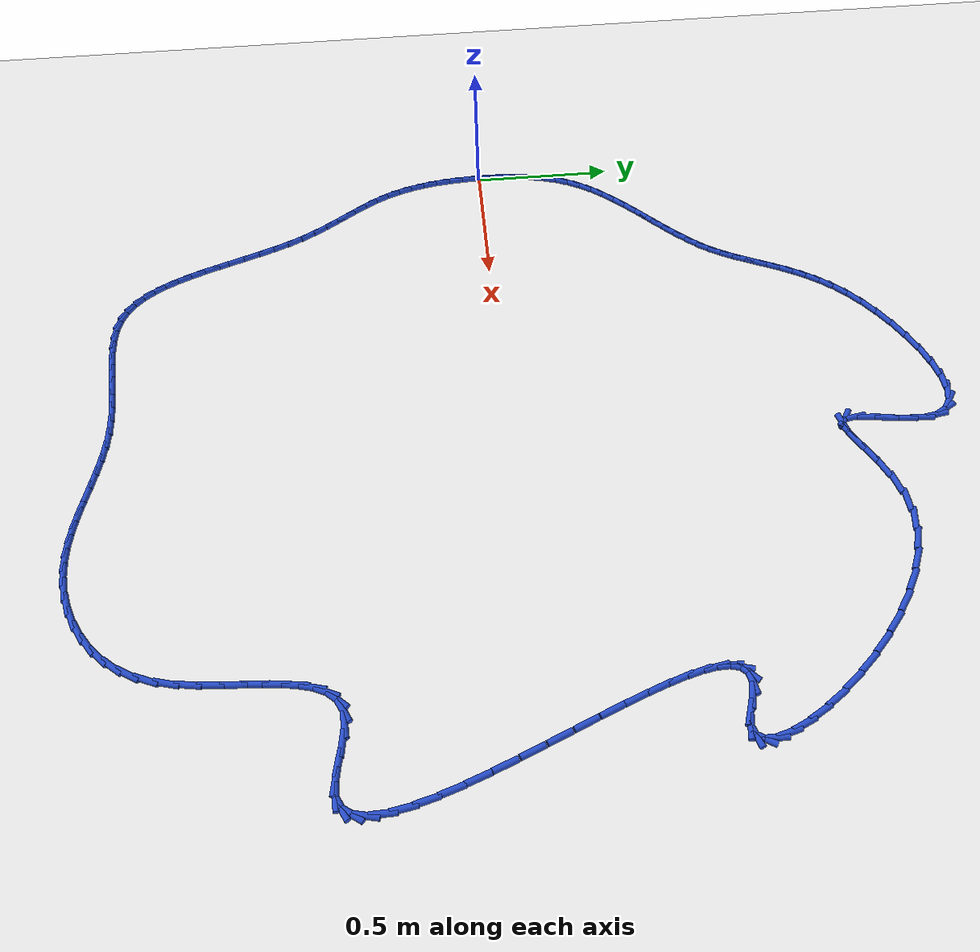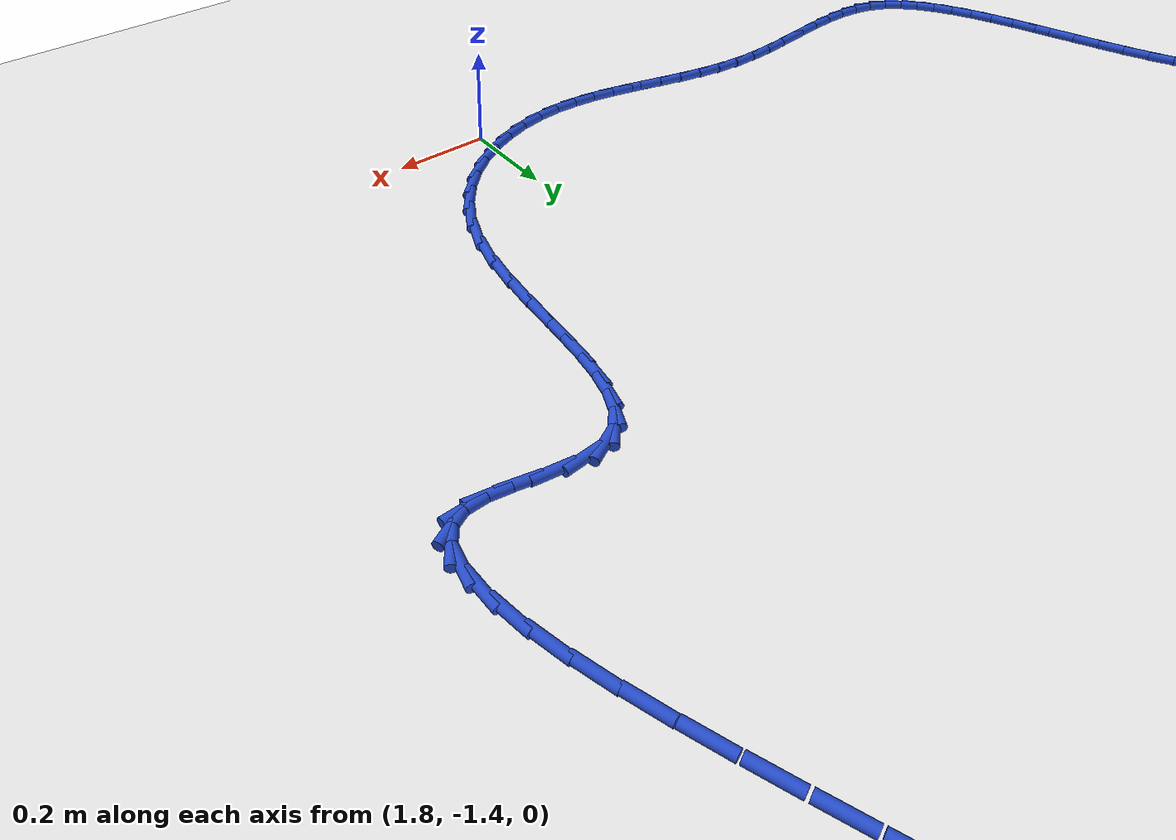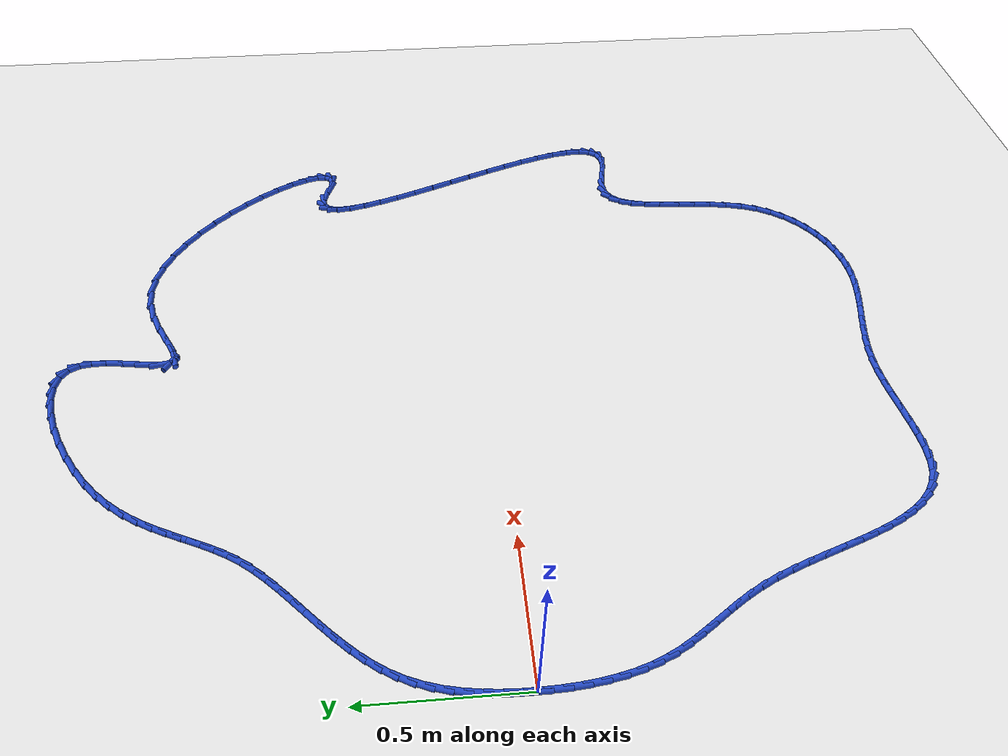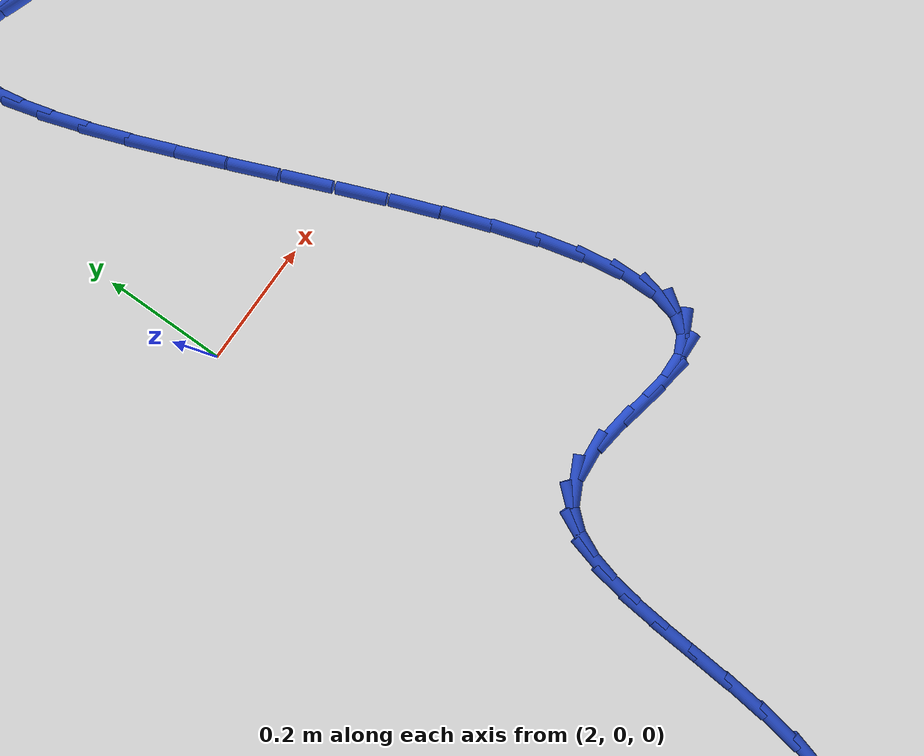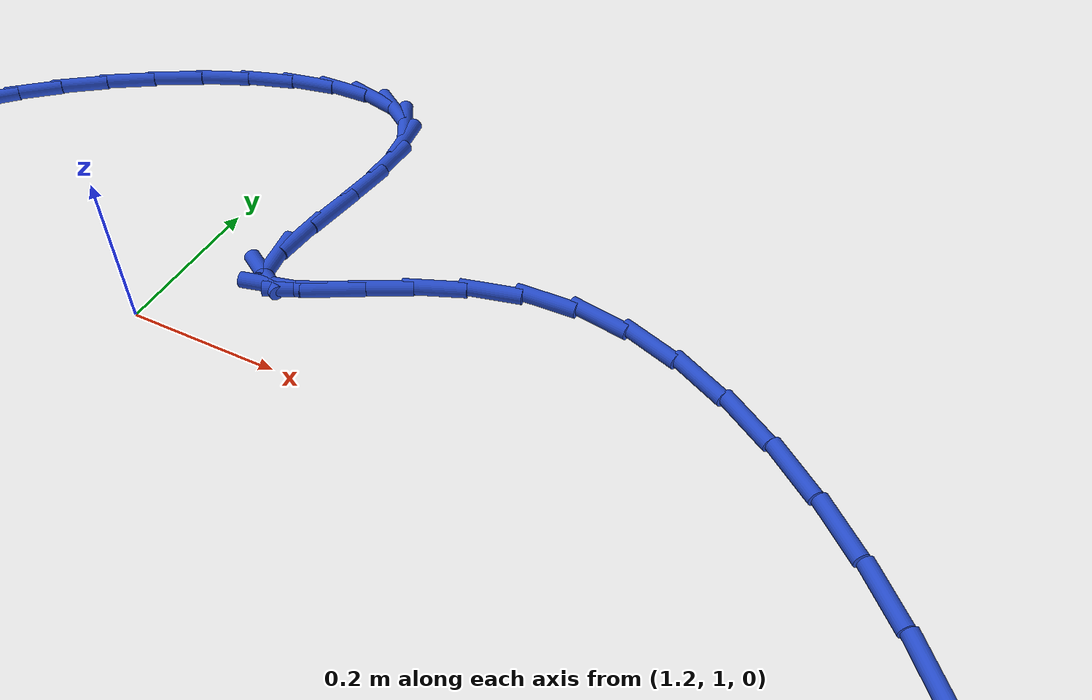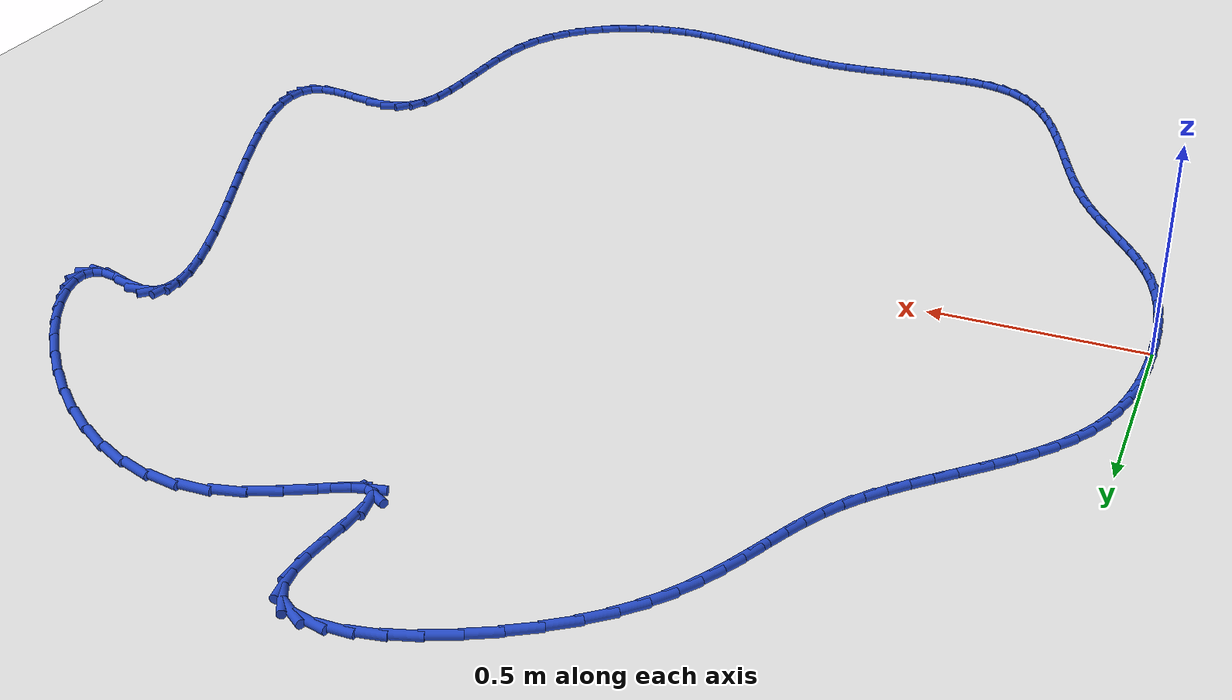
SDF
<sdf version="1.6">
 <world name="default">
  <light name="sun" type="directional">
   <pose>0 0 10 0 -0 0</pose>
   <diffuse>0.8 0.8 0.8 1</diffuse>
   <specular>0.2 0.2 0.2 1</specular>
   <attenuation>
    <range>1000</range>
    <constant>0.9</constant>
    <linear>0.01</linear>
    <quadratic>0.001</quadratic>
   </attenuation>
   <direction>-0.5 0.1 -0.9</direction>
  </light>
  <model name="ground_plane">
   <static>1</static>
   <link name="link">
    <collision name="collision">
     <geometry><plane><normal>0 0 1</normal><size>100 100</size></plane></geometry>
     <surface><friction><ode><mu>100</mu><mu2>50</mu2></ode></friction></surface>
    </collision>
    <visual name="visual">
     <cast_shadows>0</cast_shadows>
     <geometry><plane><normal>0 0 1</normal><size>100 100</size></plane></geometry>
     <material>
      <script><uri>file://media/materials/scripts/gazebo.material</uri><name>Gazebo/WhiteGlow</name></script>
     </material>
    </visual>
   </link>
  </model>
  <gravity>0 0 -9.8</gravity>
  <magnetic_field>6e-06 2.3e-05 -4.2e-05</magnetic_field>
  <atmosphere type="adiabatic"/>
  <physics name="default_physics" default="0" type="ode">
   <max_step_size>0.001</max_step_size>
   <real_time_factor>1</real_time_factor>
   <real_time_update_rate>1000</real_time_update_rate>
  </physics>
  <scene><ambient>0.4 0.4 0.4 1</ambient><background>0.7 0.7 0.7 1</background><shadows>1</shadows></scene>
  <spherical_coordinates>
   <surface_model>EARTH_WGS84</surface_model>
   <latitude_deg>0</latitude_deg>
   <longitude_deg>0</longitude_deg>
   <elevation>0</elevation>
   <heading_deg>0</heading_deg>
  </spherical_coordinates>
  <model name="line">
   <link name="link_0">
    <pose>5.204170427930421e-18 -8.326672684688674e-17 0.01 0 1.57 1.5625860259602238</pose>
    <collision name="collision">
     <geometry><cylinder><radius>0.01</radius><length>0.08</length></cylinder></geometry>
    </collision>
    <visual name="visual">
     <material>
      <script><name>Gazebo/Blue</name><uri>file://media/materials/scripts/gazebo.material</uri></script>
     </material>
     <geometry><cylinder><radius>0.01</radius><length>0.08</length></cylinder></geometry>
    </visual>
   </link>
   <link name="link_1">
    <pose>0.00043500452021122795 0.052981584294443676 0.01 0 1.57 1.5208898642054383</pose>
    <collision name="collision">
     <geometry><cylinder><radius>0.01</radius><length>0.08</length></cylinder></geometry>
    </collision>
    <visual name="visual">
     <material>
      <script><name>Gazebo/Blue</name><uri>file://media/materials/scripts/gazebo.material</uri></script>
     </material>
     <geometry><cylinder><radius>0.01</radius><length>0.08</length></cylinder></geometry>
    </visual>
   </link>
   <link name="link_2">
    <pose>0.0030667140822659717 0.10567063836101559 0.01 0 1.57 1.470550214013936</pose>
    <collision name="collision">
     <geometry><cylinder><radius>0.01</radius><length>0.08</length></cylinder></geometry>
    </collision>
    <visual name="visual">
     <material>
      <script><name>Gazebo/Blue</name><uri>file://media/materials/scripts/gazebo.material</uri></script>
     </material>
     <geometry><cylinder><radius>0.01</radius><length>0.08</length></cylinder></geometry>
    </visual>
   </link>
   <link name="link_3">
    <pose>0.008303527528725279 0.15773509716535003 0.01 0 1.57 1.410747370872445</pose>
    <collision name="collision">
     <geometry><cylinder><radius>0.01</radius><length>0.08</length></cylinder></geometry>
    </collision>
    <visual name="visual">
     <material>
      <script><name>Gazebo/Blue</name><uri>file://media/materials/scripts/gazebo.material</uri></script>
     </material>
     <geometry><cylinder><radius>0.01</radius><length>0.08</length></cylinder></geometry>
    </visual>
   </link>
   <link name="link_4">
    <pose>0.016553843702150194 0.2088428956730814 0.01 0 1.57 1.3406552772887717</pose>
    <collision name="collision">
     <geometry><cylinder><radius>0.01</radius><length>0.08</length></cylinder></geometry>
    </collision>
    <visual name="visual">
     <material>
      <script><name>Gazebo/Blue</name><uri>file://media/materials/scripts/gazebo.material</uri></script>
     </material>
     <geometry><cylinder><radius>0.01</radius><length>0.08</length></cylinder></geometry>
    </visual>
   </link>
   <link name="link_5">
    <pose>0.02822606144510177 0.25866196884984394 0.01 0 1.57 1.2596060054157323</pose>
    <collision name="collision">
     <geometry><cylinder><radius>0.01</radius><length>0.08</length></cylinder></geometry>
    </collision>
    <visual name="visual">
     <material>
      <script><name>Gazebo/Blue</name><uri>file://media/materials/scripts/gazebo.material</uri></script>
     </material>
     <geometry><cylinder><radius>0.01</radius><length>0.08</length></cylinder></geometry>
    </visual>
   </link>
   <link name="link_6">
    <pose>0.04372857960014104 0.3068602516612719 0.01 0 1.57 1.1673349412045655</pose>
    <collision name="collision">
     <geometry><cylinder><radius>0.01</radius><length>0.08</length></cylinder></geometry>
    </collision>
    <visual name="visual">
     <material>
      <script><name>Gazebo/Blue</name><uri>file://media/materials/scripts/gazebo.material</uri></script>
     </material>
     <geometry><cylinder><radius>0.01</radius><length>0.08</length></cylinder></geometry>
    </visual>
   </link>
   <link name="link_7">
    <pose>0.06346979700982908 0.3531056790729997 0.01 0 1.57 1.066675365331074</pose>
    <collision name="collision">
     <geometry><cylinder><radius>0.01</radius><length>0.08</length></cylinder></geometry>
    </collision>
    <visual name="visual">
     <material>
      <script><name>Gazebo/Blue</name><uri>file://media/materials/scripts/gazebo.material</uri></script>
     </material>
     <geometry><cylinder><radius>0.01</radius><length>0.08</length></cylinder></geometry>
    </visual>
   </link>
   <link name="link_8">
    <pose>0.08775436303835932 0.3971261382254803 0.01 0 1.57 0.9753920985315021</pose>
    <collision name="collision">
     <geometry><cylinder><radius>0.01</radius><length>0.08</length></cylinder></geometry>
    </collision>
    <visual name="visual">
     <material>
      <script><name>Gazebo/Blue</name><uri>file://media/materials/scripts/gazebo.material</uri></script>
     </material>
     <geometry><cylinder><radius>0.01</radius><length>0.08</length></cylinder></geometry>
    </visual>
   </link>
   <link name="link_9">
    <pose>0.11616525586093962 0.43906653770317067 0.01 0 1.57 0.9011191690737261</pose>
    <collision name="collision">
     <geometry><cylinder><radius>0.01</radius><length>0.08</length></cylinder></geometry>
    </collision>
    <visual name="visual">
     <material>
      <script><name>Gazebo/Blue</name><uri>file://media/materials/scripts/gazebo.material</uri></script>
     </material>
     <geometry><cylinder><radius>0.01</radius><length>0.08</length></cylinder></geometry>
    </visual>
   </link>
   <link name="link_10">
    <pose>0.14797884102928566 0.479248963787172 0.01 0 1.57 0.8434396431426506</pose>
    <collision name="collision">
     <geometry><cylinder><radius>0.01</radius><length>0.08</length></cylinder></geometry>
    </collision>
    <visual name="visual">
     <material>
      <script><name>Gazebo/Blue</name><uri>file://media/materials/scripts/gazebo.material</uri></script>
     </material>
     <geometry><cylinder><radius>0.01</radius><length>0.08</length></cylinder></geometry>
    </visual>
   </link>
   <link name="link_11">
    <pose>0.18247036417398113 0.5179961499108268 0.01 0 1.57 0.8014602633661414</pose>
    <collision name="collision">
     <geometry><cylinder><radius>0.01</radius><length>0.08</length></cylinder></geometry>
    </collision>
    <visual name="visual">
     <material>
      <script><name>Gazebo/Blue</name><uri>file://media/materials/scripts/gazebo.material</uri></script>
     </material>
     <geometry><cylinder><radius>0.01</radius><length>0.08</length></cylinder></geometry>
    </visual>
   </link>
   <link name="link_12">
    <pose>0.21891507092560988 0.5556308295074779 0.01 0 1.57 0.7742841384340893</pose>
    <collision name="collision">
     <geometry><cylinder><radius>0.01</radius><length>0.08</length></cylinder></geometry>
    </collision>
    <visual name="visual">
     <material>
      <script><name>Gazebo/Blue</name><uri>file://media/materials/scripts/gazebo.material</uri></script>
     </material>
     <geometry><cylinder><radius>0.01</radius><length>0.08</length></cylinder></geometry>
    </visual>
   </link>
   <link name="link_13">
    <pose>0.2565882069147555 0.5924757360104675 0.01 0 1.57 0.7612736541619016</pose>
    <collision name="collision">
     <geometry><cylinder><radius>0.01</radius><length>0.08</length></cylinder></geometry>
    </collision>
    <visual name="visual">
     <material>
      <script><name>Gazebo/Blue</name><uri>file://media/materials/scripts/gazebo.material</uri></script>
     </material>
     <geometry><cylinder><radius>0.01</radius><length>0.08</length></cylinder></geometry>
    </visual>
   </link>
   <link name="link_14">
    <pose>0.29476501777200187 0.6288536028531385 0.01 0 1.57 0.7621891333284874</pose>
    <collision name="collision">
     <geometry><cylinder><radius>0.01</radius><length>0.08</length></cylinder></geometry>
    </collision>
    <visual name="visual">
     <material>
      <script><name>Gazebo/Blue</name><uri>file://media/materials/scripts/gazebo.material</uri></script>
     </material>
     <geometry><cylinder><radius>0.01</radius><length>0.08</length></cylinder></geometry>
    </visual>
   </link>
   <link name="link_15">
    <pose>0.3327207491279326 0.665087163468833 0.01 0 1.57 0.7772548632885544</pose>
    <collision name="collision">
     <geometry><cylinder><radius>0.01</radius><length>0.08</length></cylinder></geometry>
    </collision>
    <visual name="visual">
     <material>
      <script><name>Gazebo/Blue</name><uri>file://media/materials/scripts/gazebo.material</uri></script>
     </material>
     <geometry><cylinder><radius>0.01</radius><length>0.08</length></cylinder></geometry>
    </visual>
   </link>
   <link name="link_16">
    <pose>0.36973064661313176 0.7014991512908944 0.01 0 1.57 0.8071772200619033</pose>
    <collision name="collision">
     <geometry><cylinder><radius>0.01</radius><length>0.08</length></cylinder></geometry>
    </collision>
    <visual name="visual">
     <material>
      <script><name>Gazebo/Blue</name><uri>file://media/materials/scripts/gazebo.material</uri></script>
     </material>
     <geometry><cylinder><radius>0.01</radius><length>0.08</length></cylinder></geometry>
    </visual>
   </link>
   <link name="link_17">
    <pose>0.40506995585818284 0.7384122997526644 0.01 0 1.57 0.8531072843763111</pose>
    <collision name="collision">
     <geometry><cylinder><radius>0.01</radius><length>0.08</length></cylinder></geometry>
    </collision>
    <visual name="visual">
     <material>
      <script><name>Gazebo/Blue</name><uri>file://media/materials/scripts/gazebo.material</uri></script>
     </material>
     <geometry><cylinder><radius>0.01</radius><length>0.08</length></cylinder></geometry>
    </visual>
   </link>
   <link name="link_18">
    <pose>0.43801392249366966 0.7761493422874861 0.01 0 1.57 0.9165021651937806</pose>
    <collision name="collision">
     <geometry><cylinder><radius>0.01</radius><length>0.08</length></cylinder></geometry>
    </collision>
    <visual name="visual">
     <material>
      <script><name>Gazebo/Blue</name><uri>file://media/materials/scripts/gazebo.material</uri></script>
     </material>
     <geometry><cylinder><radius>0.01</radius><length>0.08</length></cylinder></geometry>
    </visual>
   </link>
   <link name="link_19">
    <pose>0.4678377921501757 0.8150330123287015 0.01 0 1.57 0.9941278987002673</pose>
    <collision name="collision">
     <geometry><cylinder><radius>0.01</radius><length>0.08</length></cylinder></geometry>
    </collision>
    <visual name="visual">
     <material>
      <script><name>Gazebo/Blue</name><uri>file://media/materials/scripts/gazebo.material</uri></script>
     </material>
     <geometry><cylinder><radius>0.01</radius><length>0.08</length></cylinder></geometry>
    </visual>
   </link>
   <link name="link_20">
    <pose>0.4940388525267223 0.8553164822280097 0.01 0 1.57 1.0611538157828693</pose>
    <collision name="collision">
     <geometry><cylinder><radius>0.01</radius><length>0.08</length></cylinder></geometry>
    </collision>
    <visual name="visual">
     <material>
      <script><name>Gazebo/Blue</name><uri>file://media/materials/scripts/gazebo.material</uri></script>
     </material>
     <geometry><cylinder><radius>0.01</radius><length>0.08</length></cylinder></geometry>
    </visual>
   </link>
   <link name="link_21">
    <pose>0.5172737059981456 0.8968897355802032 0.01 0 1.57 1.107431508202331</pose>
    <collision name="collision">
     <geometry><cylinder><radius>0.01</radius><length>0.08</length></cylinder></geometry>
    </collision>
    <visual name="visual">
     <material>
      <script><name>Gazebo/Blue</name><uri>file://media/materials/scripts/gazebo.material</uri></script>
     </material>
     <geometry><cylinder><radius>0.01</radius><length>0.08</length></cylinder></geometry>
    </visual>
   </link>
   <link name="link_22">
    <pose>0.538576075469526 0.9395246120977981 0.01 0 1.57 1.1319307226415518</pose>
    <collision name="collision">
     <geometry><cylinder><radius>0.01</radius><length>0.08</length></cylinder></geometry>
    </collision>
    <visual name="visual">
     <material>
      <script><name>Gazebo/Blue</name><uri>file://media/materials/scripts/gazebo.material</uri></script>
     </material>
     <geometry><cylinder><radius>0.01</radius><length>0.08</length></cylinder></geometry>
    </visual>
   </link>
   <link name="link_23">
    <pose>0.5589798863942435 0.9829928880392141 0.01 0 1.57 1.134699054621189</pose>
    <collision name="collision">
     <geometry><cylinder><radius>0.01</radius><length>0.08</length></cylinder></geometry>
    </collision>
    <visual name="visual">
     <material>
      <script><name>Gazebo/Blue</name><uri>file://media/materials/scripts/gazebo.material</uri></script>
     </material>
     <geometry><cylinder><radius>0.01</radius><length>0.08</length></cylinder></geometry>
    </visual>
   </link>
   <link name="link_24">
    <pose>0.579519064225678 1.0270663396628705 0.01 0 1.57 1.116491813912213</pose>
    <collision name="collision">
     <geometry><cylinder><radius>0.01</radius><length>0.08</length></cylinder></geometry>
    </collision>
    <visual name="visual">
     <material>
      <script><name>Gazebo/Blue</name><uri>file://media/materials/scripts/gazebo.material</uri></script>
     </material>
     <geometry><cylinder><radius>0.01</radius><length>0.08</length></cylinder></geometry>
    </visual>
   </link>
   <link name="link_25">
    <pose>0.6012275344172092 1.0715167432271868 0.01 0 1.57 1.0786510362585258</pose>
    <collision name="collision">
     <geometry><cylinder><radius>0.01</radius><length>0.08</length></cylinder></geometry>
    </collision>
    <visual name="visual">
     <material>
      <script><name>Gazebo/Blue</name><uri>file://media/materials/scripts/gazebo.material</uri></script>
     </material>
     <geometry><cylinder><radius>0.01</radius><length>0.08</length></cylinder></geometry>
    </visual>
   </link>
   <link name="link_26">
    <pose>0.6251392224222173 1.1161158749905824 0.01 0 1.57 1.0231896917033152</pose>
    <collision name="collision">
     <geometry><cylinder><radius>0.01</radius><length>0.08</length></cylinder></geometry>
    </collision>
    <visual name="visual">
     <material>
      <script><name>Gazebo/Blue</name><uri>file://media/materials/scripts/gazebo.material</uri></script>
     </material>
     <geometry><cylinder><radius>0.01</radius><length>0.08</length></cylinder></geometry>
    </visual>
   </link>
   <link name="link_27">
    <pose>0.652288053694082 1.1606355112114763 0.01 0 1.57 0.952947877245439</pose>
    <collision name="collision">
     <geometry><cylinder><radius>0.01</radius><length>0.08</length></cylinder></geometry>
    </collision>
    <visual name="visual">
     <material>
      <script><name>Gazebo/Blue</name><uri>file://media/materials/scripts/gazebo.material</uri></script>
     </material>
     <geometry><cylinder><radius>0.01</radius><length>0.08</length></cylinder></geometry>
    </visual>
   </link>
   <link name="link_28">
    <pose>0.6837079536861835 1.204847428148289 0.01 0 1.57 0.8716390027845998</pose>
    <collision name="collision">
     <geometry><cylinder><radius>0.01</radius><length>0.08</length></cylinder></geometry>
    </collision>
    <visual name="visual">
     <material>
      <script><name>Gazebo/Blue</name><uri>file://media/materials/scripts/gazebo.material</uri></script>
     </material>
     <geometry><cylinder><radius>0.01</radius><length>0.08</length></cylinder></geometry>
    </visual>
   </link>
   <link name="link_29">
    <pose>0.7204328478519013 1.248523402059439 0.01 0 1.57 0.7836301448735291</pose>
    <collision name="collision">
     <geometry><cylinder><radius>0.01</radius><length>0.08</length></cylinder></geometry>
    </collision>
    <visual name="visual">
     <material>
      <script><name>Gazebo/Blue</name><uri>file://media/materials/scripts/gazebo.material</uri></script>
     </material>
     <geometry><cylinder><radius>0.01</radius><length>0.08</length></cylinder></geometry>
    </visual>
   </link>
   <link name="link_30">
    <pose>0.7634966616446157 1.2914352092033465 0.01 0 1.57 0.6948969449313782</pose>
    <collision name="collision">
     <geometry><cylinder><radius>0.01</radius><length>0.08</length></cylinder></geometry>
    </collision>
    <visual name="visual">
     <material>
      <script><name>Gazebo/Blue</name><uri>file://media/materials/scripts/gazebo.material</uri></script>
     </material>
     <geometry><cylinder><radius>0.01</radius><length>0.08</length></cylinder></geometry>
    </visual>
   </link>
   <link name="link_31">
    <pose>0.8136782272785172 1.3332666739318826 0.01 0 1.57 0.6161848446954908</pose>
    <collision name="collision">
     <geometry><cylinder><radius>0.01</radius><length>0.08</length></cylinder></geometry>
    </collision>
    <visual name="visual">
     <material>
      <script><name>Gazebo/Blue</name><uri>file://media/materials/scripts/gazebo.material</uri></script>
     </material>
     <geometry><cylinder><radius>0.01</radius><length>0.08</length></cylinder></geometry>
    </visual>
   </link>
   <link name="link_32">
    <pose>0.8698466300683007 1.3730431716259925 0.01 0 1.57 0.5447257016983517</pose>
    <collision name="collision">
     <geometry><cylinder><radius>0.01</radius><length>0.08</length></cylinder></geometry>
    </collision>
    <visual name="visual">
     <material>
      <script><name>Gazebo/Blue</name><uri>file://media/materials/scripts/gazebo.material</uri></script>
     </material>
     <geometry><cylinder><radius>0.01</radius><length>0.08</length></cylinder></geometry>
    </visual>
   </link>
   <link name="link_33">
    <pose>0.9300053398819851 1.4094916278562137 0.01 0 1.57 0.4735326778670908</pose>
    <collision name="collision">
     <geometry><cylinder><radius>0.01</radius><length>0.08</length></cylinder></geometry>
    </collision>
    <visual name="visual">
     <material>
      <script><name>Gazebo/Blue</name><uri>file://media/materials/scripts/gazebo.material</uri></script>
     </material>
     <geometry><cylinder><radius>0.01</radius><length>0.08</length></cylinder></geometry>
    </visual>
   </link>
   <link name="link_34">
    <pose>0.9921535321259036 1.441337487534113 0.01 0 1.57 0.39586508999717585</pose>
    <collision name="collision">
     <geometry><cylinder><radius>0.01</radius><length>0.08</length></cylinder></geometry>
    </collision>
    <visual name="visual">
     <material>
      <script><name>Gazebo/Blue</name><uri>file://media/materials/scripts/gazebo.material</uri></script>
     </material>
     <geometry><cylinder><radius>0.01</radius><length>0.08</length></cylinder></geometry>
    </visual>
   </link>
   <link name="link_35">
    <pose>1.0542903822063896 1.4673061955712574 0.01 0 1.57 0.30330965088102346</pose>
    <collision name="collision">
     <geometry><cylinder><radius>0.01</radius><length>0.08</length></cylinder></geometry>
    </collision>
    <visual name="visual">
     <material>
      <script><name>Gazebo/Blue</name><uri>file://media/materials/scripts/gazebo.material</uri></script>
     </material>
     <geometry><cylinder><radius>0.01</radius><length>0.08</length></cylinder></geometry>
    </visual>
   </link>
   <link name="link_36">
    <pose>1.1144150655297766 1.4861231968792137 0.01 0 1.57 0.18310539684767244</pose>
    <collision name="collision">
     <geometry><cylinder><radius>0.01</radius><length>0.08</length></cylinder></geometry>
    </collision>
    <visual name="visual">
     <material>
      <script><name>Gazebo/Blue</name><uri>file://media/materials/scripts/gazebo.material</uri></script>
     </material>
     <geometry><cylinder><radius>0.01</radius><length>0.08</length></cylinder></geometry>
    </visual>
   </link>
   <link name="link_37">
    <pose>1.1705267575023979 1.4965139363695494 0.01 0 1.57 0.013770623196092291</pose>
    <collision name="collision">
     <geometry><cylinder><radius>0.01</radius><length>0.08</length></cylinder></geometry>
    </collision>
    <visual name="visual">
     <material>
      <script><name>Gazebo/Blue</name><uri>file://media/materials/scripts/gazebo.material</uri></script>
     </material>
     <geometry><cylinder><radius>0.01</radius><length>0.08</length></cylinder></geometry>
    </visual>
   </link>
   <link name="link_38">
    <pose>1.2206246335305855 1.4972038589538306 0.01 0 1.57 -0.23970804611762409</pose>
    <collision name="collision">
     <geometry><cylinder><radius>0.01</radius><length>0.08</length></cylinder></geometry>
    </collision>
    <visual name="visual">
     <material>
      <script><name>Gazebo/Blue</name><uri>file://media/materials/scripts/gazebo.material</uri></script>
     </material>
     <geometry><cylinder><radius>0.01</radius><length>0.08</length></cylinder></geometry>
    </visual>
   </link>
   <link name="link_39">
    <pose>1.262707869020674 1.4869184095436245 0.01 0 1.57 -0.612564018022563</pose>
    <collision name="collision">
     <geometry><cylinder><radius>0.01</radius><length>0.08</length></cylinder></geometry>
    </collision>
    <visual name="visual">
     <material>
      <script><name>Gazebo/Blue</name><uri>file://media/materials/scripts/gazebo.material</uri></script>
     </material>
     <geometry><cylinder><radius>0.01</radius><length>0.08</length></cylinder></geometry>
    </visual>
   </link>
   <link name="link_40">
    <pose>1.294775639378996 1.4643830330504986 0.01 0 1.57 -1.063311678665787</pose>
    <collision name="collision">
     <geometry><cylinder><radius>0.01</radius><length>0.08</length></cylinder></geometry>
    </collision>
    <visual name="visual">
     <material>
      <script><name>Gazebo/Blue</name><uri>file://media/materials/scripts/gazebo.material</uri></script>
     </material>
     <geometry><cylinder><radius>0.01</radius><length>0.08</length></cylinder></geometry>
    </visual>
   </link>
   <link name="link_41">
    <pose>1.3148271200118848 1.4283231743860185 0.01 0 1.57 -1.4334432177207181</pose>
    <collision name="collision">
     <geometry><cylinder><radius>0.01</radius><length>0.08</length></cylinder></geometry>
    </collision>
    <visual name="visual">
     <material>
      <script><name>Gazebo/Blue</name><uri>file://media/materials/scripts/gazebo.material</uri></script>
     </material>
     <geometry><cylinder><radius>0.01</radius><length>0.08</length></cylinder></geometry>
    </visual>
   </link>
   <link name="link_42">
    <pose>1.3217228671589292 1.378434767908933 0.01 0 1.57 1.5209047134766496</pose>
    <collision name="collision">
     <geometry><cylinder><radius>0.01</radius><length>0.08</length></cylinder></geometry>
    </collision>
    <visual name="visual">
     <material>
      <script><name>Gazebo/Blue</name><uri>file://media/materials/scripts/gazebo.material</uri></script>
     </material>
     <geometry><cylinder><radius>0.01</radius><length>0.08</length></cylinder></geometry>
    </visual>
   </link>
   <link name="link_43">
    <pose>1.3187766296948247 1.3194310136191352 0.01 0 1.57 1.4414093233951701</pose>
    <collision name="collision">
     <geometry><cylinder><radius>0.01</radius><length>0.08</length></cylinder></geometry>
    </collision>
    <visual name="visual">
     <material>
      <script><name>Gazebo/Blue</name><uri>file://media/materials/scripts/gazebo.material</uri></script>
     </material>
     <geometry><cylinder><radius>0.01</radius><length>0.08</length></cylinder></geometry>
    </visual>
   </link>
   <link name="link_44">
    <pose>1.3107369787073733 1.2576416785013402 0.01 0 1.57 1.4278364744829437</pose>
    <collision name="collision">
     <geometry><cylinder><radius>0.01</radius><length>0.08</length></cylinder></geometry>
    </collision>
    <visual name="visual">
     <material>
      <script><name>Gazebo/Blue</name><uri>file://media/materials/scripts/gazebo.material</uri></script>
     </material>
     <geometry><cylinder><radius>0.01</radius><length>0.08</length></cylinder></geometry>
    </visual>
   </link>
   <link name="link_45">
    <pose>1.302353180068665 1.1993973123308643 0.01 0 1.57 1.4887240151860532</pose>
    <collision name="collision">
     <geometry><cylinder><radius>0.01</radius><length>0.08</length></cylinder></geometry>
    </collision>
    <visual name="visual">
     <material>
      <script><name>Gazebo/Blue</name><uri>file://media/materials/scripts/gazebo.material</uri></script>
     </material>
     <geometry><cylinder><radius>0.01</radius><length>0.08</length></cylinder></geometry>
    </visual>
   </link>
   <link name="link_46">
    <pose>1.2983744996507915 1.1510284648830267 0.01 0 1.57 -1.41124205783127</pose>
    <collision name="collision">
     <geometry><cylinder><radius>0.01</radius><length>0.08</length></cylinder></geometry>
    </collision>
    <visual name="visual">
     <material>
      <script><name>Gazebo/Blue</name><uri>file://media/materials/scripts/gazebo.material</uri></script>
     </material>
     <geometry><cylinder><radius>0.01</radius><length>0.08</length></cylinder></geometry>
    </visual>
   </link>
   <link name="link_47">
    <pose>1.3035502033258426 1.1188656859331423 0.01 0 1.57 -0.5428448192312582</pose>
    <collision name="collision">
     <geometry><cylinder><radius>0.01</radius><length>0.08</length></cylinder></geometry>
    </collision>
    <visual name="visual">
     <material>
      <script><name>Gazebo/Blue</name><uri>file://media/materials/scripts/gazebo.material</uri></script>
     </material>
     <geometry><cylinder><radius>0.01</radius><length>0.08</length></cylinder></geometry>
    </visual>
   </link>
   <link name="link_48">
    <pose>1.3218466099721702 1.107827404392785 0.01 0 1.57 0.22862839273643384</pose>
    <collision name="collision">
     <geometry><cylinder><radius>0.01</radius><length>0.08</length></cylinder></geometry>
    </collision>
    <visual name="visual">
     <material>
      <script><name>Gazebo/Blue</name><uri>file://media/materials/scripts/gazebo.material</uri></script>
     </material>
     <geometry><cylinder><radius>0.01</radius><length>0.08</length></cylinder></geometry>
    </visual>
   </link>
   <link name="link_49">
    <pose>1.352919753709203 1.1150580324323875 0.01 0 1.57 0.4438074241718497</pose>
    <collision name="collision">
     <geometry><cylinder><radius>0.01</radius><length>0.08</length></cylinder></geometry>
    </collision>
    <visual name="visual">
     <material>
      <script><name>Gazebo/Blue</name><uri>file://media/materials/scripts/gazebo.material</uri></script>
     </material>
     <geometry><cylinder><radius>0.01</radius><length>0.08</length></cylinder></geometry>
    </visual>
   </link>
   <link name="link_50">
    <pose>1.394950323565977 1.1350410542157272 0.01 0 1.57 0.4888503084165558</pose>
    <collision name="collision">
     <geometry><cylinder><radius>0.01</radius><length>0.08</length></cylinder></geometry>
    </collision>
    <visual name="visual">
     <material>
      <script><name>Gazebo/Blue</name><uri>file://media/materials/scripts/gazebo.material</uri></script>
     </material>
     <geometry><cylinder><radius>0.01</radius><length>0.08</length></cylinder></geometry>
    </visual>
   </link>
   <link name="link_51">
    <pose>1.446117712373408 1.1622576160875184 0.01 0 1.57 0.45939053684366965</pose>
    <collision name="collision">
     <geometry><cylinder><radius>0.01</radius><length>0.08</length></cylinder></geometry>
    </collision>
    <visual name="visual">
     <material>
      <script><name>Gazebo/Blue</name><uri>file://media/materials/scripts/gazebo.material</uri></script>
     </material>
     <geometry><cylinder><radius>0.01</radius><length>0.08</length></cylinder></geometry>
    </visual>
   </link>
   <link name="link_52">
    <pose>1.5046013129624147 1.1911888643924782 0.01 0 1.57 0.37423061509577554</pose>
    <collision name="collision">
     <geometry><cylinder><radius>0.01</radius><length>0.08</length></cylinder></geometry>
    </collision>
    <visual name="visual">
     <material>
      <script><name>Gazebo/Blue</name><uri>file://media/materials/scripts/gazebo.material</uri></script>
     </material>
     <geometry><cylinder><radius>0.01</radius><length>0.08</length></cylinder></geometry>
    </visual>
   </link>
   <link name="link_53">
    <pose>1.5685805181639132 1.2163159454753214 0.01 0 1.57 0.22948535530560002</pose>
    <collision name="collision">
     <geometry><cylinder><radius>0.01</radius><length>0.08</length></cylinder></geometry>
    </collision>
    <visual name="visual">
     <material>
      <script><name>Gazebo/Blue</name><uri>file://media/materials/scripts/gazebo.material</uri></script>
     </material>
     <geometry><cylinder><radius>0.01</radius><length>0.08</length></cylinder></geometry>
    </visual>
   </link>
   <link name="link_54">
    <pose>1.6362347208088217 1.2321200056807644 0.01 0 1.57 0.02602913116310797</pose>
    <collision name="collision">
     <geometry><cylinder><radius>0.01</radius><length>0.08</length></cylinder></geometry>
    </collision>
    <visual name="visual">
     <material>
      <script><name>Gazebo/Blue</name><uri>file://media/materials/scripts/gazebo.material</uri></script>
     </material>
     <geometry><cylinder><radius>0.01</radius><length>0.08</length></cylinder></geometry>
    </visual>
   </link>
   <link name="link_55">
    <pose>1.7058501896405012 1.2339324451871763 0.01 0 1.57 -0.16971665434272856</pose>
    <collision name="collision">
     <geometry><cylinder><radius>0.01</radius><length>0.08</length></cylinder></geometry>
    </collision>
    <visual name="visual">
     <material>
      <script><name>Gazebo/Blue</name><uri>file://media/materials/scripts/gazebo.material</uri></script>
     </material>
     <geometry><cylinder><radius>0.01</radius><length>0.08</length></cylinder></geometry>
    </visual>
   </link>
   <link name="link_56">
    <pose>1.776313139789273 1.2218575517566421 0.01 0 1.57 -0.33099004219598527</pose>
    <collision name="collision">
     <geometry><cylinder><radius>0.01</radius><length>0.08</length></cylinder></geometry>
    </collision>
    <visual name="visual">
     <material>
      <script><name>Gazebo/Blue</name><uri>file://media/materials/scripts/gazebo.material</uri></script>
     </material>
     <geometry><cylinder><radius>0.01</radius><length>0.08</length></cylinder></geometry>
    </visual>
   </link>
   <link name="link_57">
    <pose>1.8467189840494924 1.1976638900848264 0.01 0 1.57 -0.4615714933665127</pose>
    <collision name="collision">
     <geometry><cylinder><radius>0.01</radius><length>0.08</length></cylinder></geometry>
    </collision>
    <visual name="visual">
     <material>
      <script><name>Gazebo/Blue</name><uri>file://media/materials/scripts/gazebo.material</uri></script>
     </material>
     <geometry><cylinder><radius>0.01</radius><length>0.08</length></cylinder></geometry>
    </visual>
   </link>
   <link name="link_58">
    <pose>1.9161633505988465 1.1631217383545416 0.01 0 1.57 -0.5679484792166528</pose>
    <collision name="collision">
     <geometry><cylinder><radius>0.01</radius><length>0.08</length></cylinder></geometry>
    </collision>
    <visual name="visual">
     <material>
      <script><name>Gazebo/Blue</name><uri>file://media/materials/scripts/gazebo.material</uri></script>
     </material>
     <geometry><cylinder><radius>0.01</radius><length>0.08</length></cylinder></geometry>
    </visual>
   </link>
   <link name="link_59">
    <pose>1.9837418676150191 1.1200013747486022 0.01 0 1.57 -0.6564296513133588</pose>
    <collision name="collision">
     <geometry><cylinder><radius>0.01</radius><length>0.08</length></cylinder></geometry>
    </collision>
    <visual name="visual">
     <material>
      <script><name>Gazebo/Blue</name><uri>file://media/materials/scripts/gazebo.material</uri></script>
     </material>
     <geometry><cylinder><radius>0.01</radius><length>0.08</length></cylinder></geometry>
    </visual>
   </link>
   <link name="link_60">
    <pose>2.048550163275696 1.0700730774498202 0.01 0 1.57 -0.7323234388851076</pose>
    <collision name="collision">
     <geometry><cylinder><radius>0.01</radius><length>0.08</length></cylinder></geometry>
    </collision>
    <visual name="visual">
     <material>
      <script><name>Gazebo/Blue</name><uri>file://media/materials/scripts/gazebo.material</uri></script>
     </material>
     <geometry><cylinder><radius>0.01</radius><length>0.08</length></cylinder></geometry>
    </visual>
   </link>
   <link name="link_61">
    <pose>2.1096838657585644 1.015107124641009 0.01 0 1.57 -0.8000205283445078</pose>
    <collision name="collision">
     <geometry><cylinder><radius>0.01</radius><length>0.08</length></cylinder></geometry>
    </collision>
    <visual name="visual">
     <material>
      <script><name>Gazebo/Blue</name><uri>file://media/materials/scripts/gazebo.material</uri></script>
     </material>
     <geometry><cylinder><radius>0.01</radius><length>0.08</length></cylinder></geometry>
    </visual>
   </link>
   <link name="link_62">
    <pose>2.1662386032413075 0.9568737945049828 0.01 0 1.57 -0.8633884399972575</pose>
    <collision name="collision">
     <geometry><cylinder><radius>0.01</radius><length>0.08</length></cylinder></geometry>
    </collision>
    <visual name="visual">
     <material>
      <script><name>Gazebo/Blue</name><uri>file://media/materials/scripts/gazebo.material</uri></script>
     </material>
     <geometry><cylinder><radius>0.01</radius><length>0.08</length></cylinder></geometry>
    </visual>
   </link>
   <link name="link_63">
    <pose>2.217310003901612 0.8971433652245531 0.01 0 1.57 -0.9263190505667785</pose>
    <collision name="collision">
     <geometry><cylinder><radius>0.01</radius><length>0.08</length></cylinder></geometry>
    </collision>
    <visual name="visual">
     <material>
      <script><name>Gazebo/Blue</name><uri>file://media/materials/scripts/gazebo.material</uri></script>
     </material>
     <geometry><cylinder><radius>0.01</radius><length>0.08</length></cylinder></geometry>
    </visual>
   </link>
   <link name="link_64">
    <pose>2.2619936959171634 0.837686114982535 0.01 0 1.57 -0.9935321250354436</pose>
    <collision name="collision">
     <geometry><cylinder><radius>0.01</radius><length>0.08</length></cylinder></geometry>
    </collision>
    <visual name="visual">
     <material>
      <script><name>Gazebo/Blue</name><uri>file://media/materials/scripts/gazebo.material</uri></script>
     </material>
     <geometry><cylinder><radius>0.01</radius><length>0.08</length></cylinder></geometry>
    </visual>
   </link>
   <link name="link_65">
    <pose>2.2993853074656476 0.7802723219617409 0.01 0 1.57 -1.0720427152715077</pose>
    <collision name="collision">
     <geometry><cylinder><radius>0.01</radius><length>0.08</length></cylinder></geometry>
    </collision>
    <visual name="visual">
     <material>
      <script><name>Gazebo/Blue</name><uri>file://media/materials/scripts/gazebo.material</uri></script>
     </material>
     <geometry><cylinder><radius>0.01</radius><length>0.08</length></cylinder></geometry>
    </visual>
   </link>
   <link name="link_66">
    <pose>2.3285804667247505 0.7266722643449836 0.01 0 1.57 -1.1744508160605993</pose>
    <collision name="collision">
     <geometry><cylinder><radius>0.01</radius><length>0.08</length></cylinder></geometry>
    </collision>
    <visual name="visual">
     <material>
      <script><name>Gazebo/Blue</name><uri>file://media/materials/scripts/gazebo.material</uri></script>
     </material>
     <geometry><cylinder><radius>0.01</radius><length>0.08</length></cylinder></geometry>
    </visual>
   </link>
   <link name="link_67">
    <pose>2.348674801872156 0.678656220315077 0.01 0 1.57 -1.327584491817045</pose>
    <collision name="collision">
     <geometry><cylinder><radius>0.01</radius><length>0.08</length></cylinder></geometry>
    </collision>
    <visual name="visual">
     <material>
      <script><name>Gazebo/Blue</name><uri>file://media/materials/scripts/gazebo.material</uri></script>
     </material>
     <geometry><cylinder><radius>0.01</radius><length>0.08</length></cylinder></geometry>
    </visual>
   </link>
   <link name="link_68">
    <pose>2.3587639410855514 0.6379944680548337 0.01 0 1.57 1.5447875498582477</pose>
    <collision name="collision">
     <geometry><cylinder><radius>0.01</radius><length>0.08</length></cylinder></geometry>
    </collision>
    <visual name="visual">
     <material>
      <script><name>Gazebo/Blue</name><uri>file://media/materials/scripts/gazebo.material</uri></script>
     </material>
     <geometry><cylinder><radius>0.01</radius><length>0.08</length></cylinder></geometry>
    </visual>
   </link>
   <link name="link_69">
    <pose>2.357943512542621 0.6064572857470674 0.01 0 1.57 1.0215555971413368</pose>
    <collision name="collision">
     <geometry><cylinder><radius>0.01</radius><length>0.08</length></cylinder></geometry>
    </collision>
    <visual name="visual">
     <material>
      <script><name>Gazebo/Blue</name><uri>file://media/materials/scripts/gazebo.material</uri></script>
     </material>
     <geometry><cylinder><radius>0.01</radius><length>0.08</length></cylinder></geometry>
    </visual>
   </link>
   <link name="link_70">
    <pose>2.3453091444210514 0.5858149515745914 0.01 0 1.57 0.304841928672054</pose>
    <collision name="collision">
     <geometry><cylinder><radius>0.01</radius><length>0.08</length></cylinder></geometry>
    </collision>
    <visual name="visual">
     <material>
      <script><name>Gazebo/Blue</name><uri>file://media/materials/scripts/gazebo.material</uri></script>
     </material>
     <geometry><cylinder><radius>0.01</radius><length>0.08</length></cylinder></geometry>
    </visual>
   </link>
   <link name="link_71">
    <pose>2.3199564648985276 0.5778377437202187 0.01 0 1.57 -0.16417871830335745</pose>
    <collision name="collision">
     <geometry><cylinder><radius>0.01</radius><length>0.08</length></cylinder></geometry>
    </collision>
    <visual name="visual">
     <material>
      <script><name>Gazebo/Blue</name><uri>file://media/materials/scripts/gazebo.material</uri></script>
     </material>
     <geometry><cylinder><radius>0.01</radius><length>0.08</length></cylinder></geometry>
    </visual>
   </link>
   <link name="link_72">
    <pose>2.2809822563960886 0.5842945979223737 0.01 0 1.57 -0.339017712695943</pose>
    <collision name="collision">
     <geometry><cylinder><radius>0.01</radius><length>0.08</length></cylinder></geometry>
    </collision>
    <visual name="visual">
     <material>
      <script><name>Gazebo/Blue</name><uri>file://media/materials/scripts/gazebo.material</uri></script>
     </material>
     <geometry><cylinder><radius>0.01</radius><length>0.08</length></cylinder></geometry>
    </visual>
   </link>
   <link name="link_73">
    <pose>2.2321653281250224 0.6015090119443703 0.01 0 1.57 -0.21023803896432322</pose>
    <collision name="collision">
     <geometry><cylinder><radius>0.01</radius><length>0.08</length></cylinder></geometry>
    </collision>
    <visual name="visual">
     <material>
      <script><name>Gazebo/Blue</name><uri>file://media/materials/scripts/gazebo.material</uri></script>
     </material>
     <geometry><cylinder><radius>0.01</radius><length>0.08</length></cylinder></geometry>
    </visual>
   </link>
   <link name="link_74">
    <pose>2.19046096827154 0.6104083599269372 0.01 0 1.57 0.17801262102497437</pose>
    <collision name="collision">
     <geometry><cylinder><radius>0.01</radius><length>0.08</length></cylinder></geometry>
    </collision>
    <visual name="visual">
     <material>
      <script><name>Gazebo/Blue</name><uri>file://media/materials/scripts/gazebo.material</uri></script>
     </material>
     <geometry><cylinder><radius>0.01</radius><length>0.08</length></cylinder></geometry>
    </visual>
   </link>
   <link name="link_75">
    <pose>2.1610547805544993 0.6051176844485274 0.01 0 1.57 0.786646414998817</pose>
    <collision name="collision">
     <geometry><cylinder><radius>0.01</radius><length>0.08</length></cylinder></geometry>
    </collision>
    <visual name="visual">
     <material>
      <script><name>Gazebo/Blue</name><uri>file://media/materials/scripts/gazebo.material</uri></script>
     </material>
     <geometry><cylinder><radius>0.01</radius><length>0.08</length></cylinder></geometry>
    </visual>
   </link>
   <link name="link_76">
    <pose>2.1428473582274634 0.586864750399621 0.01 0 1.57 1.3058316351920345</pose>
    <collision name="collision">
     <geometry><cylinder><radius>0.01</radius><length>0.08</length></cylinder></geometry>
    </collision>
    <visual name="visual">
     <material>
      <script><name>Gazebo/Blue</name><uri>file://media/materials/scripts/gazebo.material</uri></script>
     </material>
     <geometry><cylinder><radius>0.01</radius><length>0.08</length></cylinder></geometry>
    </visual>
   </link>
   <link name="link_77">
    <pose>2.134717204219437 0.5569022870589012 0.01 0 1.57 -1.5503728362421276</pose>
    <collision name="collision">
     <geometry><cylinder><radius>0.01</radius><length>0.08</length></cylinder></geometry>
    </collision>
    <visual name="visual">
     <material>
      <script><name>Gazebo/Blue</name><uri>file://media/materials/scripts/gazebo.material</uri></script>
     </material>
     <geometry><cylinder><radius>0.01</radius><length>0.08</length></cylinder></geometry>
    </visual>
   </link>
   <link name="link_78">
    <pose>2.135542821459423 0.5164830237050526 0.01 0 1.57 -1.398023726576133</pose>
    <collision name="collision">
     <geometry><cylinder><radius>0.01</radius><length>0.08</length></cylinder></geometry>
    </collision>
    <visual name="visual">
     <material>
      <script><name>Gazebo/Blue</name><uri>file://media/materials/scripts/gazebo.material</uri></script>
     </material>
     <geometry><cylinder><radius>0.01</radius><length>0.08</length></cylinder></geometry>
    </visual>
   </link>
   <link name="link_79">
    <pose>2.1442027128764263 0.4668596896167587 0.01 0 1.57 -1.3098790261121023</pose>
    <collision name="collision">
     <geometry><cylinder><radius>0.01</radius><length>0.08</length></cylinder></geometry>
    </collision>
    <visual name="visual">
     <material>
      <script><name>Gazebo/Blue</name><uri>file://media/materials/scripts/gazebo.material</uri></script>
     </material>
     <geometry><cylinder><radius>0.01</radius><length>0.08</length></cylinder></geometry>
    </visual>
   </link>
   <link name="link_80">
    <pose>2.1595753813994487 0.4092850140727042 0.01 0 1.57 -1.255507547069866</pose>
    <collision name="collision">
     <geometry><cylinder><radius>0.01</radius><length>0.08</length></cylinder></geometry>
    </collision>
    <visual name="visual">
     <material>
      <script><name>Gazebo/Blue</name><uri>file://media/materials/scripts/gazebo.material</uri></script>
     </material>
     <geometry><cylinder><radius>0.01</radius><length>0.08</length></cylinder></geometry>
    </visual>
   </link>
   <link name="link_81">
    <pose>2.1805393299574956 0.3450117263515726 0.01 0 1.57 -1.2209957160388847</pose>
    <collision name="collision">
     <geometry><cylinder><radius>0.01</radius><length>0.08</length></cylinder></geometry>
    </collision>
    <visual name="visual">
     <material>
      <script><name>Gazebo/Blue</name><uri>file://media/materials/scripts/gazebo.material</uri></script>
     </material>
     <geometry><cylinder><radius>0.01</radius><length>0.08</length></cylinder></geometry>
    </visual>
   </link>
   <link name="link_82">
    <pose>2.2059730614795705 0.2752925557320474 0.01 0 1.57 -1.1994545871882898</pose>
    <collision name="collision">
     <geometry><cylinder><radius>0.01</radius><length>0.08</length></cylinder></geometry>
    </collision>
    <visual name="visual">
     <material>
      <script><name>Gazebo/Blue</name><uri>file://media/materials/scripts/gazebo.material</uri></script>
     </material>
     <geometry><cylinder><radius>0.01</radius><length>0.08</length></cylinder></geometry>
    </visual>
   </link>
   <link name="link_83">
    <pose>2.2347550788946773 0.201380231492814 0.01 0 1.57 -1.1872906533970116</pose>
    <collision name="collision">
     <geometry><cylinder><radius>0.01</radius><length>0.08</length></cylinder></geometry>
    </collision>
    <visual name="visual">
     <material>
      <script><name>Gazebo/Blue</name><uri>file://media/materials/scripts/gazebo.material</uri></script>
     </material>
     <geometry><cylinder><radius>0.01</radius><length>0.08</length></cylinder></geometry>
    </visual>
   </link>
   <link name="link_84">
    <pose>2.26576388513182 0.124527482912555 0.01 0 1.57 -1.1826530432598252</pose>
    <collision name="collision">
     <geometry><cylinder><radius>0.01</radius><length>0.08</length></cylinder></geometry>
    </collision>
    <visual name="visual">
     <material>
      <script><name>Gazebo/Blue</name><uri>file://media/materials/scripts/gazebo.material</uri></script>
     </material>
     <geometry><cylinder><radius>0.01</radius><length>0.08</length></cylinder></geometry>
    </visual>
   </link>
   <link name="link_85">
    <pose>2.2978779831200025 0.045987039269955746 0.01 0 1.57 -1.1847600676417922</pose>
    <collision name="collision">
     <geometry><cylinder><radius>0.01</radius><length>0.08</length></cylinder></geometry>
    </collision>
    <visual name="visual">
     <material>
      <script><name>Gazebo/Blue</name><uri>file://media/materials/scripts/gazebo.material</uri></script>
     </material>
     <geometry><cylinder><radius>0.01</radius><length>0.08</length></cylinder></geometry>
    </visual>
   </link>
   <link name="link_86">
    <pose>2.329975875788228 -0.03298837015630041 0.01 0 1.57 -1.1936350038603252</pose>
    <collision name="collision">
     <geometry><cylinder><radius>0.01</radius><length>0.08</length></cylinder></geometry>
    </collision>
    <visual name="visual">
     <material>
      <script><name>Gazebo/Blue</name><uri>file://media/materials/scripts/gazebo.material</uri></script>
     </material>
     <geometry><cylinder><radius>0.01</radius><length>0.08</length></cylinder></geometry>
    </visual>
   </link>
   <link name="link_87">
    <pose>2.3609360660655008 -0.11114601608752936 0.01 0 1.57 -1.210087739164891</pose>
    <collision name="collision">
     <geometry><cylinder><radius>0.01</radius><length>0.08</length></cylinder></geometry>
    </collision>
    <visual name="visual">
     <material>
      <script><name>Gazebo/Blue</name><uri>file://media/materials/scripts/gazebo.material</uri></script>
     </material>
     <geometry><cylinder><radius>0.01</radius><length>0.08</length></cylinder></geometry>
    </visual>
   </link>
   <link name="link_88">
    <pose>2.3896370568808245 -0.18723316924504735 0.01 0 1.57 -1.2359234012138243</pose>
    <collision name="collision">
     <geometry><cylinder><radius>0.01</radius><length>0.08</length></cylinder></geometry>
    </collision>
    <visual name="visual">
     <material>
      <script><name>Gazebo/Blue</name><uri>file://media/materials/scripts/gazebo.material</uri></script>
     </material>
     <geometry><cylinder><radius>0.01</radius><length>0.08</length></cylinder></geometry>
    </visual>
   </link>
   <link name="link_89">
    <pose>2.414957351163203 -0.2599971003501713 0.01 0 1.57 -1.2744801029397066</pose>
    <collision name="collision">
     <geometry><cylinder><radius>0.01</radius><length>0.08</length></cylinder></geometry>
    </collision>
    <visual name="visual">
     <material>
      <script><name>Gazebo/Blue</name><uri>file://media/materials/scripts/gazebo.material</uri></script>
     </material>
     <geometry><cylinder><radius>0.01</radius><length>0.08</length></cylinder></geometry>
    </visual>
   </link>
   <link name="link_90">
    <pose>2.435775451841641 -0.32818508012421505 0.01 0 1.57 -1.3317944263722794</pose>
    <collision name="collision">
     <geometry><cylinder><radius>0.01</radius><length>0.08</length></cylinder></geometry>
    </collision>
    <visual name="visual">
     <material>
      <script><name>Gazebo/Blue</name><uri>file://media/materials/scripts/gazebo.material</uri></script>
     </material>
     <geometry><cylinder><radius>0.01</radius><length>0.08</length></cylinder></geometry>
    </visual>
   </link>
   <link name="link_91">
    <pose>2.450969861845141 -0.3905443792884954 0.01 0 1.57 -1.4191203203108913</pose>
    <collision name="collision">
     <geometry><cylinder><radius>0.01</radius><length>0.08</length></cylinder></geometry>
    </collision>
    <visual name="visual">
     <material>
      <script><name>Gazebo/Blue</name><uri>file://media/materials/scripts/gazebo.material</uri></script>
     </material>
     <geometry><cylinder><radius>0.01</radius><length>0.08</length></cylinder></geometry>
    </visual>
   </link>
   <link name="link_92">
    <pose>2.4594190841027075 -0.44582226856432855 0.01 0 1.57 -1.558387698587088</pose>
    <collision name="collision">
     <geometry><cylinder><radius>0.01</radius><length>0.08</length></cylinder></geometry>
    </collision>
    <visual name="visual">
     <material>
      <script><name>Gazebo/Blue</name><uri>file://media/materials/scripts/gazebo.material</uri></script>
     </material>
     <geometry><cylinder><radius>0.01</radius><length>0.08</length></cylinder></geometry>
    </visual>
   </link>
   <link name="link_93">
    <pose>2.460001621543344 -0.4927660186730306 0.01 0 1.57 1.3494730668818262</pose>
    <collision name="collision">
     <geometry><cylinder><radius>0.01</radius><length>0.08</length></cylinder></geometry>
    </collision>
    <visual name="visual">
     <material>
      <script><name>Gazebo/Blue</name><uri>file://media/materials/scripts/gazebo.material</uri></script>
     </material>
     <geometry><cylinder><radius>0.01</radius><length>0.08</length></cylinder></geometry>
    </visual>
   </link>
   <link name="link_94">
    <pose>2.451595977096055 -0.5301229003359181 0.01 0 1.57 0.9612552075482939</pose>
    <collision name="collision">
     <geometry><cylinder><radius>0.01</radius><length>0.08</length></cylinder></geometry>
    </collision>
    <visual name="visual">
     <material>
      <script><name>Gazebo/Blue</name><uri>file://media/materials/scripts/gazebo.material</uri></script>
     </material>
     <geometry><cylinder><radius>0.01</radius><length>0.08</length></cylinder></geometry>
    </visual>
   </link>
   <link name="link_95">
    <pose>2.433080653689843 -0.5566401842743055 0.01 0 1.57 0.4515187346285411</pose>
    <collision name="collision">
     <geometry><cylinder><radius>0.01</radius><length>0.08</length></cylinder></geometry>
    </collision>
    <visual name="visual">
     <material>
      <script><name>Gazebo/Blue</name><uri>file://media/materials/scripts/gazebo.material</uri></script>
     </material>
     <geometry><cylinder><radius>0.01</radius><length>0.08</length></cylinder></geometry>
    </visual>
   </link>
   <link name="link_96">
    <pose>2.403334154253714 -0.5710651412095098 0.01 0 1.57 0.03258134605563192</pose>
    <collision name="collision">
     <geometry><cylinder><radius>0.01</radius><length>0.08</length></cylinder></geometry>
    </collision>
    <visual name="visual">
     <material>
      <script><name>Gazebo/Blue</name><uri>file://media/materials/scripts/gazebo.material</uri></script>
     </material>
     <geometry><cylinder><radius>0.01</radius><length>0.08</length></cylinder></geometry>
    </visual>
   </link>
   <link name="link_97">
    <pose>2.3614778585872913 -0.572429358422973 0.01 0 1.57 -0.16104470599386742</pose>
    <collision name="collision">
     <geometry><cylinder><radius>0.01</radius><length>0.08</length></cylinder></geometry>
    </collision>
    <visual name="visual">
     <material>
      <script><name>Gazebo/Blue</name><uri>file://media/materials/scripts/gazebo.material</uri></script>
     </material>
     <geometry><cylinder><radius>0.01</radius><length>0.08</length></cylinder></geometry>
    </visual>
   </link>
   <link name="link_98">
    <pose>2.310358045713449 -0.564124865305195 0.01 0 1.57 -0.2017016225229833</pose>
    <collision name="collision">
     <geometry><cylinder><radius>0.01</radius><length>0.08</length></cylinder></geometry>
    </collision>
    <visual name="visual">
     <material>
      <script><name>Gazebo/Blue</name><uri>file://media/materials/scripts/gazebo.material</uri></script>
     </material>
     <geometry><cylinder><radius>0.01</radius><length>0.08</length></cylinder></geometry>
    </visual>
   </link>
   <link name="link_99">
    <pose>2.2557355594351978 -0.5529555395236839 0.01 0 1.57 -0.13570200149633832</pose>
    <collision name="collision">
     <geometry><cylinder><radius>0.01</radius><length>0.08</length></cylinder></geometry>
    </collision>
    <visual name="visual">
     <material>
      <script><name>Gazebo/Blue</name><uri>file://media/materials/scripts/gazebo.material</uri></script>
     </material>
     <geometry><cylinder><radius>0.01</radius><length>0.08</length></cylinder></geometry>
    </visual>
   </link>
   <link name="link_100">
    <pose>2.20344898991319 -0.545816270199244 0.01 0 1.57 0.08147625548266185</pose>
    <collision name="collision">
     <geometry><cylinder><radius>0.01</radius><length>0.08</length></cylinder></geometry>
    </collision>
    <visual name="visual">
     <material>
      <script><name>Gazebo/Blue</name><uri>file://media/materials/scripts/gazebo.material</uri></script>
     </material>
     <geometry><cylinder><radius>0.01</radius><length>0.08</length></cylinder></geometry>
    </visual>
   </link>
   <link name="link_101">
    <pose>2.159189379211113 -0.5494303783645761 0.01 0 1.57 0.4631856962183469</pose>
    <collision name="collision">
     <geometry><cylinder><radius>0.01</radius><length>0.08</length></cylinder></geometry>
    </collision>
    <visual name="visual">
     <material>
      <script><name>Gazebo/Blue</name><uri>file://media/materials/scripts/gazebo.material</uri></script>
     </material>
     <geometry><cylinder><radius>0.01</radius><length>0.08</length></cylinder></geometry>
    </visual>
   </link>
   <link name="link_102">
    <pose>2.1251358139967502 -0.5664375032891009 0.01 0 1.57 0.852377505354001</pose>
    <collision name="collision">
     <geometry><cylinder><radius>0.01</radius><length>0.08</length></cylinder></geometry>
    </collision>
    <visual name="visual">
     <material>
      <script><name>Gazebo/Blue</name><uri>file://media/materials/scripts/gazebo.material</uri></script>
     </material>
     <geometry><cylinder><radius>0.01</radius><length>0.08</length></cylinder></geometry>
    </visual>
   </link>
   <link name="link_103">
    <pose>2.099888389896904 -0.5953156538120642 0.01 0 1.57 1.1387334216762603</pose>
    <collision name="collision">
     <geometry><cylinder><radius>0.01</radius><length>0.08</length></cylinder></geometry>
    </collision>
    <visual name="visual">
     <material>
      <script><name>Gazebo/Blue</name><uri>file://media/materials/scripts/gazebo.material</uri></script>
     </material>
     <geometry><cylinder><radius>0.01</radius><length>0.08</length></cylinder></geometry>
    </visual>
   </link>
   <link name="link_104">
    <pose>2.0818862458098004 -0.6343556792040228 0.01 0 1.57 1.3170277254615903</pose>
    <collision name="collision">
     <geometry><cylinder><radius>0.01</radius><length>0.08</length></cylinder></geometry>
    </collision>
    <visual name="visual">
     <material>
      <script><name>Gazebo/Blue</name><uri>file://media/materials/scripts/gazebo.material</uri></script>
     </material>
     <geometry><cylinder><radius>0.01</radius><length>0.08</length></cylinder></geometry>
    </visual>
   </link>
   <link name="link_105">
    <pose>2.0695685206336663 -0.6818484287355313 0.01 0 1.57 1.420847721844174</pose>
    <collision name="collision">
     <geometry><cylinder><radius>0.01</radius><length>0.08</length></cylinder></geometry>
    </collision>
    <visual name="visual">
     <material>
      <script><name>Gazebo/Blue</name><uri>file://media/materials/scripts/gazebo.material</uri></script>
     </material>
     <geometry><cylinder><radius>0.01</radius><length>0.08</length></cylinder></geometry>
    </visual>
   </link>
   <link name="link_106">
    <pose>2.0613743532667286 -0.736084751677146 0.01 0 1.57 1.476068043122643</pose>
    <collision name="collision">
     <geometry><cylinder><radius>0.01</radius><length>0.08</length></cylinder></geometry>
    </collision>
    <visual name="visual">
     <material>
      <script><name>Gazebo/Blue</name><uri>file://media/materials/scripts/gazebo.material</uri></script>
     </material>
     <geometry><cylinder><radius>0.01</radius><length>0.08</length></cylinder></geometry>
    </visual>
   </link>
   <link name="link_107">
    <pose>2.0557428826072144 -0.7953554972994241 0.01 0 1.57 1.496970207896974</pose>
    <collision name="collision">
     <geometry><cylinder><radius>0.01</radius><length>0.08</length></cylinder></geometry>
    </collision>
    <visual name="visual">
     <material>
      <script><name>Gazebo/Blue</name><uri>file://media/materials/scripts/gazebo.material</uri></script>
     </material>
     <geometry><cylinder><radius>0.01</radius><length>0.08</length></cylinder></geometry>
    </visual>
   </link>
   <link name="link_108">
    <pose>2.05111324755335 -0.8579515148729207 0.01 0 1.57 1.4901665321780844</pose>
    <collision name="collision">
     <geometry><cylinder><radius>0.01</radius><length>0.08</length></cylinder></geometry>
    </collision>
    <visual name="visual">
     <material>
      <script><name>Gazebo/Blue</name><uri>file://media/materials/scripts/gazebo.material</uri></script>
     </material>
     <geometry><cylinder><radius>0.01</radius><length>0.08</length></cylinder></geometry>
    </visual>
   </link>
   <link name="link_109">
    <pose>2.045924587003363 -0.9221636536681925 0.01 0 1.57 1.457302237332466</pose>
    <collision name="collision">
     <geometry><cylinder><radius>0.01</radius><length>0.08</length></cylinder></geometry>
    </collision>
    <visual name="visual">
     <material>
      <script><name>Gazebo/Blue</name><uri>file://media/materials/scripts/gazebo.material</uri></script>
     </material>
     <geometry><cylinder><radius>0.01</radius><length>0.08</length></cylinder></geometry>
    </visual>
   </link>
   <link name="link_110">
    <pose>2.038616039855479 -0.9862827629557962 0.01 0 1.57 1.396245676788558</pose>
    <collision name="collision">
     <geometry><cylinder><radius>0.01</radius><length>0.08</length></cylinder></geometry>
    </collision>
    <visual name="visual">
     <material>
      <script><name>Gazebo/Blue</name><uri>file://media/materials/scripts/gazebo.material</uri></script>
     </material>
     <geometry><cylinder><radius>0.01</radius><length>0.08</length></cylinder></geometry>
    </visual>
   </link>
   <link name="link_111">
    <pose>2.027626745007927 -1.048599692006286 0.01 0 1.57 1.301491835406188</pose>
    <collision name="collision">
     <geometry><cylinder><radius>0.01</radius><length>0.08</length></cylinder></geometry>
    </collision>
    <visual name="visual">
     <material>
      <script><name>Gazebo/Blue</name><uri>file://media/materials/scripts/gazebo.material</uri></script>
     </material>
     <geometry><cylinder><radius>0.01</radius><length>0.08</length></cylinder></geometry>
    </visual>
   </link>
   <link name="link_112">
    <pose>2.011395841358932 -1.1074052900902194 0.01 0 1.57 1.168344797253381</pose>
    <collision name="collision">
     <geometry><cylinder><radius>0.01</radius><length>0.08</length></cylinder></geometry>
    </collision>
    <visual name="visual">
     <material>
      <script><name>Gazebo/Blue</name><uri>file://media/materials/scripts/gazebo.material</uri></script>
     </material>
     <geometry><cylinder><radius>0.01</radius><length>0.08</length></cylinder></geometry>
    </visual>
   </link>
   <link name="link_113">
    <pose>1.9885339986485766 -1.1611111769204756 0.01 0 1.57 1.0219003645880327</pose>
    <collision name="collision">
     <geometry><cylinder><radius>0.01</radius><length>0.08</length></cylinder></geometry>
    </collision>
    <visual name="visual">
     <material>
      <script><name>Gazebo/Blue</name><uri>file://media/materials/scripts/gazebo.material</uri></script>
     </material>
     <geometry><cylinder><radius>0.01</radius><length>0.08</length></cylinder></geometry>
    </visual>
   </link>
   <link name="link_114">
    <pose>1.9591384141489 -1.2091755979107108 0.01 0 1.57 0.8799530599385964</pose>
    <collision name="collision">
     <geometry><cylinder><radius>0.01</radius><length>0.08</length></cylinder></geometry>
    </collision>
    <visual name="visual">
     <material>
      <script><name>Gazebo/Blue</name><uri>file://media/materials/scripts/gazebo.material</uri></script>
     </material>
     <geometry><cylinder><radius>0.01</radius><length>0.08</length></cylinder></geometry>
    </visual>
   </link>
   <link name="link_115">
    <pose>1.924068973284617 -1.2515937875347285 0.01 0 1.57 0.7449028266580465</pose>
    <collision name="collision">
     <geometry><cylinder><radius>0.01</radius><length>0.08</length></cylinder></geometry>
    </collision>
    <visual name="visual">
     <material>
      <script><name>Gazebo/Blue</name><uri>file://media/materials/scripts/gazebo.material</uri></script>
     </material>
     <geometry><cylinder><radius>0.01</radius><length>0.08</length></cylinder></geometry>
    </visual>
   </link>
   <link name="link_116">
    <pose>1.8841917841028424 -1.2883653614542914 0.01 0 1.57 0.6176062180739855</pose>
    <collision name="collision">
     <geometry><cylinder><radius>0.01</radius><length>0.08</length></cylinder></geometry>
    </collision>
    <visual name="visual">
     <material>
      <script><name>Gazebo/Blue</name><uri>file://media/materials/scripts/gazebo.material</uri></script>
     </material>
     <geometry><cylinder><radius>0.01</radius><length>0.08</length></cylinder></geometry>
    </visual>
   </link>
   <link name="link_117">
    <pose>1.8403729546506875 -1.3194899353311638 0.01 0 1.57 0.4976761927513409</pose>
    <collision name="collision">
     <geometry><cylinder><radius>0.01</radius><length>0.08</length></cylinder></geometry>
    </collision>
    <visual name="visual">
     <material>
      <script><name>Gazebo/Blue</name><uri>file://media/materials/scripts/gazebo.material</uri></script>
     </material>
     <geometry><cylinder><radius>0.01</radius><length>0.08</length></cylinder></geometry>
    </visual>
   </link>
   <link name="link_118">
    <pose>1.7934785929752646 -1.3449671248271093 0.01 0 1.57 0.3838009143368715</pose>
    <collision name="collision">
     <geometry><cylinder><radius>0.01</radius><length>0.08</length></cylinder></geometry>
    </collision>
    <visual name="visual">
     <material>
      <script><name>Gazebo/Blue</name><uri>file://media/materials/scripts/gazebo.material</uri></script>
     </material>
     <geometry><cylinder><radius>0.01</radius><length>0.08</length></cylinder></geometry>
    </visual>
   </link>
   <link name="link_119">
    <pose>1.7443748071236875 -1.3647965456038926 0.01 0 1.57 0.274039231448352</pose>
    <collision name="collision">
     <geometry><cylinder><radius>0.01</radius><length>0.08</length></cylinder></geometry>
    </collision>
    <visual name="visual">
     <material>
      <script><name>Gazebo/Blue</name><uri>file://media/materials/scripts/gazebo.material</uri></script>
     </material>
     <geometry><cylinder><radius>0.01</radius><length>0.08</length></cylinder></geometry>
    </visual>
   </link>
   <link name="link_120">
    <pose>1.6939277051430681 -1.3789778133232764 0.01 0 1.57 0.16601493133944</pose>
    <collision name="collision">
     <geometry><cylinder><radius>0.01</radius><length>0.08</length></cylinder></geometry>
    </collision>
    <visual name="visual">
     <material>
      <script><name>Gazebo/Blue</name><uri>file://media/materials/scripts/gazebo.material</uri></script>
     </material>
     <geometry><cylinder><radius>0.01</radius><length>0.08</length></cylinder></geometry>
    </visual>
   </link>
   <link name="link_121">
    <pose>1.643003395080518 -1.3875105436470259 0.01 0 1.57 0.05780334549569558</pose>
    <collision name="collision">
     <geometry><cylinder><radius>0.01</radius><length>0.08</length></cylinder></geometry>
    </collision>
    <visual name="visual">
     <material>
      <script><name>Gazebo/Blue</name><uri>file://media/materials/scripts/gazebo.material</uri></script>
     </material>
     <geometry><cylinder><radius>0.01</radius><length>0.08</length></cylinder></geometry>
    </visual>
   </link>
   <link name="link_122">
    <pose>1.5924216885892057 -1.3904375962116018 0.01 0 1.57 -0.041542558406590185</pose>
    <collision name="collision">
     <geometry><cylinder><radius>0.01</radius><length>0.08</length></cylinder></geometry>
    </collision>
    <visual name="visual">
     <material>
      <script><name>Gazebo/Blue</name><uri>file://media/materials/scripts/gazebo.material</uri></script>
     </material>
     <geometry><cylinder><radius>0.01</radius><length>0.08</length></cylinder></geometry>
    </visual>
   </link>
   <link name="link_123">
    <pose>1.542406292920057 -1.3883586326306967 0.01 0 1.57 -0.12224587214847836</pose>
    <collision name="collision">
     <geometry><cylinder><radius>0.01</radius><length>0.08</length></cylinder></geometry>
    </collision>
    <visual name="visual">
     <material>
      <script><name>Gazebo/Blue</name><uri>file://media/materials/scripts/gazebo.material</uri></script>
     </material>
     <geometry><cylinder><radius>0.01</radius><length>0.08</length></cylinder></geometry>
    </visual>
   </link>
   <link name="link_124">
    <pose>1.492766919740666 -1.3822600144962223 0.01 0 1.57 -0.18241648208774755</pose>
    <collision name="collision">
     <geometry><cylinder><radius>0.01</radius><length>0.08</length></cylinder></geometry>
    </collision>
    <visual name="visual">
     <material>
      <script><name>Gazebo/Blue</name><uri>file://media/materials/scripts/gazebo.material</uri></script>
     </material>
     <geometry><cylinder><radius>0.01</radius><length>0.08</length></cylinder></geometry>
    </visual>
   </link>
   <link name="link_125">
    <pose>1.4433049303425 -1.3731359032182466 0.01 0 1.57 -0.221732055208342</pose>
    <collision name="collision">
     <geometry><cylinder><radius>0.01</radius><length>0.08</length></cylinder></geometry>
    </collision>
    <visual name="visual">
     <material>
      <script><name>Gazebo/Blue</name><uri>file://media/materials/scripts/gazebo.material</uri></script>
     </material>
     <geometry><cylinder><radius>0.01</radius><length>0.08</length></cylinder></geometry>
    </visual>
   </link>
   <link name="link_126">
    <pose>1.3938216860170245 -1.3619804602068353 0.01 0 1.57 -0.2405584938520159</pose>
    <collision name="collision">
     <geometry><cylinder><radius>0.01</radius><length>0.08</length></cylinder></geometry>
    </collision>
    <visual name="visual">
     <material>
      <script><name>Gazebo/Blue</name><uri>file://media/materials/scripts/gazebo.material</uri></script>
     </material>
     <geometry><cylinder><radius>0.01</radius><length>0.08</length></cylinder></geometry>
    </visual>
   </link>
   <link name="link_127">
    <pose>1.3441185480557085 -1.349787846872057 0.01 0 1.57 -0.23943543039399204</pose>
    <collision name="collision">
     <geometry><cylinder><radius>0.01</radius><length>0.08</length></cylinder></geometry>
    </collision>
    <visual name="visual">
     <material>
      <script><name>Gazebo/Blue</name><uri>file://media/materials/scripts/gazebo.material</uri></script>
     </material>
     <geometry><cylinder><radius>0.01</radius><length>0.08</length></cylinder></geometry>
    </visual>
   </link>
   <link name="link_128">
    <pose>1.2939968777500175 -1.3375522246239775 0.01 0 1.57 -0.21884119515434433</pose>
    <collision name="collision">
     <geometry><cylinder><radius>0.01</radius><length>0.08</length></cylinder></geometry>
    </collision>
    <visual name="visual">
     <material>
      <script><name>Gazebo/Blue</name><uri>file://media/materials/scripts/gazebo.material</uri></script>
     </material>
     <geometry><cylinder><radius>0.01</radius><length>0.08</length></cylinder></geometry>
    </visual>
   </link>
   <link name="link_129">
    <pose>1.2432580363914185 -1.3262677548726647 0.01 0 1.57 -0.1792072021414065</pose>
    <collision name="collision">
     <geometry><cylinder><radius>0.01</radius><length>0.08</length></cylinder></geometry>
    </collision>
    <visual name="visual">
     <material>
      <script><name>Gazebo/Blue</name><uri>file://media/materials/scripts/gazebo.material</uri></script>
     </material>
     <geometry><cylinder><radius>0.01</radius><length>0.08</length></cylinder></geometry>
    </visual>
   </link>
   <link name="link_130">
    <pose>1.1917033852713783 -1.3169285990281856 0.01 0 1.57 -0.12114234039094994</pose>
    <collision name="collision">
     <geometry><cylinder><radius>0.01</radius><length>0.08</length></cylinder></geometry>
    </collision>
    <visual name="visual">
     <material>
      <script><name>Gazebo/Blue</name><uri>file://media/materials/scripts/gazebo.material</uri></script>
     </material>
     <geometry><cylinder><radius>0.01</radius><length>0.08</length></cylinder></geometry>
    </visual>
   </link>
   <link name="link_131">
    <pose>1.1391342856813622 -1.3105289185006068 0.01 0 1.57 -0.0461455205331143</pose>
    <collision name="collision">
     <geometry><cylinder><radius>0.01</radius><length>0.08</length></cylinder></geometry>
    </collision>
    <visual name="visual">
     <material>
      <script><name>Gazebo/Blue</name><uri>file://media/materials/scripts/gazebo.material</uri></script>
     </material>
     <geometry><cylinder><radius>0.01</radius><length>0.08</length></cylinder></geometry>
    </visual>
   </link>
   <link name="link_132">
    <pose>1.0853581497801412 -1.308045627819679 0.01 0 1.57 0.02812345195951831</pose>
    <collision name="collision">
     <geometry><cylinder><radius>0.01</radius><length>0.08</length></cylinder></geometry>
    </collision>
    <visual name="visual">
     <material>
      <script><name>Gazebo/Blue</name><uri>file://media/materials/scripts/gazebo.material</uri></script>
     </material>
     <geometry><cylinder><radius>0.01</radius><length>0.08</length></cylinder></geometry>
    </visual>
   </link>
   <link name="link_133">
    <pose>1.0304863640459412 -1.3095892188279004 0.01 0 1.57 0.0797138087030484</pose>
    <collision name="collision">
     <geometry><cylinder><radius>0.01</radius><length>0.08</length></cylinder></geometry>
    </collision>
    <visual name="visual">
     <material>
      <script><name>Gazebo/Blue</name><uri>file://media/materials/scripts/gazebo.material</uri></script>
     </material>
     <geometry><cylinder><radius>0.01</radius><length>0.08</length></cylinder></geometry>
    </visual>
   </link>
   <link name="link_134">
    <pose>0.9750703225537494 -1.314016022933856 0.01 0 1.57 0.10914950244660061</pose>
    <collision name="collision">
     <geometry><cylinder><radius>0.01</radius><length>0.08</length></cylinder></geometry>
    </collision>
    <visual name="visual">
     <material>
      <script><name>Gazebo/Blue</name><uri>file://media/materials/scripts/gazebo.material</uri></script>
     </material>
     <geometry><cylinder><radius>0.01</radius><length>0.08</length></cylinder></geometry>
    </visual>
   </link>
   <link name="link_135">
    <pose>0.919695848932858 -1.3200842364568994 0.01 0 1.57 0.1175949099078932</pose>
    <collision name="collision">
     <geometry><cylinder><radius>0.01</radius><length>0.08</length></cylinder></geometry>
    </collision>
    <visual name="visual">
     <material>
      <script><name>Gazebo/Blue</name><uri>file://media/materials/scripts/gazebo.material</uri></script>
     </material>
     <geometry><cylinder><radius>0.01</radius><length>0.08</length></cylinder></geometry>
    </visual>
   </link>
   <link name="link_136">
    <pose>0.8649487668125592 -1.3265520557163872 0.01 0 1.57 0.10470100532082097</pose>
    <collision name="collision">
     <geometry><cylinder><radius>0.01</radius><length>0.08</length></cylinder></geometry>
    </collision>
    <visual name="visual">
     <material>
      <script><name>Gazebo/Blue</name><uri>file://media/materials/scripts/gazebo.material</uri></script>
     </material>
     <geometry><cylinder><radius>0.01</radius><length>0.08</length></cylinder></geometry>
    </visual>
   </link>
   <link name="link_137">
    <pose>0.8114148998221481 -1.3321776770316738 0.01 0 1.57 0.06835052619520303</pose>
    <collision name="collision">
     <geometry><cylinder><radius>0.01</radius><length>0.08</length></cylinder></geometry>
    </collision>
    <visual name="visual">
     <material>
      <script><name>Gazebo/Blue</name><uri>file://media/materials/scripts/gazebo.material</uri></script>
     </material>
     <geometry><cylinder><radius>0.01</radius><length>0.08</length></cylinder></geometry>
    </visual>
   </link>
   <link name="link_138">
    <pose>0.7596800715909166 -1.335719296722115 0.01 0 1.57 0.004373113648801396</pose>
    <collision name="collision">
     <geometry><cylinder><radius>0.01</radius><length>0.08</length></cylinder></geometry>
    </collision>
    <visual name="visual">
     <material>
      <script><name>Gazebo/Blue</name><uri>file://media/materials/scripts/gazebo.material</uri></script>
     </material>
     <geometry><cylinder><radius>0.01</radius><length>0.08</length></cylinder></geometry>
    </visual>
   </link>
   <link name="link_139">
    <pose>0.7103301057481576 -1.3359351111070652 0.01 0 1.57 -0.09355665584110565</pose>
    <collision name="collision">
     <geometry><cylinder><radius>0.01</radius><length>0.08</length></cylinder></geometry>
    </collision>
    <visual name="visual">
     <material>
      <script><name>Gazebo/Blue</name><uri>file://media/materials/scripts/gazebo.material</uri></script>
     </material>
     <geometry><cylinder><radius>0.01</radius><length>0.08</length></cylinder></geometry>
    </visual>
   </link>
   <link name="link_140">
    <pose>0.6639508259231639 -1.3315833165058804 0.01 0 1.57 -0.23297640871132172</pose>
    <collision name="collision">
     <geometry><cylinder><radius>0.01</radius><length>0.08</length></cylinder></geometry>
    </collision>
    <visual name="visual">
     <material>
      <script><name>Gazebo/Blue</name><uri>file://media/materials/scripts/gazebo.material</uri></script>
     </material>
     <geometry><cylinder><radius>0.01</radius><length>0.08</length></cylinder></geometry>
    </visual>
   </link>
   <link name="link_141">
    <pose>0.6211280557452287 -1.3214221092379155 0.01 0 1.57 -0.41698813422462583</pose>
    <collision name="collision">
     <geometry><cylinder><radius>0.01</radius><length>0.08</length></cylinder></geometry>
    </collision>
    <visual name="visual">
     <material>
      <script><name>Gazebo/Blue</name><uri>file://media/materials/scripts/gazebo.material</uri></script>
     </material>
     <geometry><cylinder><radius>0.01</radius><length>0.08</length></cylinder></geometry>
    </visual>
   </link>
   <link name="link_142">
    <pose>0.58241364002198 -1.3042729829355324 0.01 0 1.57 -0.611471641254122</pose>
    <collision name="collision">
     <geometry><cylinder><radius>0.01</radius><length>0.08</length></cylinder></geometry>
    </collision>
    <visual name="visual">
     <material>
      <script><name>Gazebo/Blue</name><uri>file://media/materials/scripts/gazebo.material</uri></script>
     </material>
     <geometry><cylinder><radius>0.01</radius><length>0.08</length></cylinder></geometry>
    </visual>
   </link>
   <link name="link_143">
    <pose>0.5477978915961169 -1.280003478822115 0.01 0 1.57 -0.7801326357452844</pose>
    <collision name="collision">
     <geometry><cylinder><radius>0.01</radius><length>0.08</length></cylinder></geometry>
    </collision>
    <visual name="visual">
     <material>
      <script><name>Gazebo/Blue</name><uri>file://media/materials/scripts/gazebo.material</uri></script>
     </material>
     <geometry><cylinder><radius>0.01</radius><length>0.08</length></cylinder></geometry>
    </visual>
   </link>
   <link name="link_144">
    <pose>0.5168099732729083 -1.249340189637035 0.01 0 1.57 -0.9165276541409897</pose>
    <collision name="collision">
     <geometry><cylinder><radius>0.01</radius><length>0.08</length></cylinder></geometry>
    </collision>
    <visual name="visual">
     <material>
      <script><name>Gazebo/Blue</name><uri>file://media/materials/scripts/gazebo.material</uri></script>
     </material>
     <geometry><cylinder><radius>0.01</radius><length>0.08</length></cylinder></geometry>
    </visual>
   </link>
   <link name="link_145">
    <pose>0.4889653898453975 -1.2130351508935049 0.01 0 1.57 -1.0220494800664488</pose>
    <collision name="collision">
     <geometry><cylinder><radius>0.01</radius><length>0.08</length></cylinder></geometry>
    </collision>
    <visual name="visual">
     <material>
      <script><name>Gazebo/Blue</name><uri>file://media/materials/scripts/gazebo.material</uri></script>
     </material>
     <geometry><cylinder><radius>0.01</radius><length>0.08</length></cylinder></geometry>
    </visual>
   </link>
   <link name="link_146">
    <pose>0.4637796461066283 -1.1718403981047367 0.01 0 1.57 -1.1010756934499077</pose>
    <collision name="collision">
     <geometry><cylinder><radius>0.01</radius><length>0.08</length></cylinder></geometry>
    </collision>
    <visual name="visual">
     <material>
      <script><name>Gazebo/Blue</name><uri>file://media/materials/scripts/gazebo.material</uri></script>
     </material>
     <geometry><cylinder><radius>0.01</radius><length>0.08</length></cylinder></geometry>
    </visual>
   </link>
   <link name="link_147">
    <pose>0.44076824684964366 -1.126507966783942 0.01 0 1.57 -1.1582585305755544</pose>
    <collision name="collision">
     <geometry><cylinder><radius>0.01</radius><length>0.08</length></cylinder></geometry>
    </collision>
    <visual name="visual">
     <material>
      <script><name>Gazebo/Blue</name><uri>file://media/materials/scripts/gazebo.material</uri></script>
     </material>
     <geometry><cylinder><radius>0.01</radius><length>0.08</length></cylinder></geometry>
    </visual>
   </link>
   <link name="link_148">
    <pose>0.4194466968674879 -1.0777898924443345 0.01 0 1.57 -1.1974361238496798</pose>
    <collision name="collision">
     <geometry><cylinder><radius>0.01</radius><length>0.08</length></cylinder></geometry>
    </collision>
    <visual name="visual">
     <material>
      <script><name>Gazebo/Blue</name><uri>file://media/materials/scripts/gazebo.material</uri></script>
     </material>
     <geometry><cylinder><radius>0.01</radius><length>0.08</length></cylinder></geometry>
    </visual>
   </link>
   <link name="link_149">
    <pose>0.39933050095320405 -1.026438210599125 0.01 0 1.57 -1.221398475627899</pose>
    <collision name="collision">
     <geometry><cylinder><radius>0.01</radius><length>0.08</length></cylinder></geometry>
    </collision>
    <visual name="visual">
     <material>
      <script><name>Gazebo/Blue</name><uri>file://media/materials/scripts/gazebo.material</uri></script>
     </material>
     <geometry><cylinder><radius>0.01</radius><length>0.08</length></cylinder></geometry>
    </visual>
   </link>
   <link name="link_150">
    <pose>0.3799351638998357 -0.9732049567615264 0.01 0 1.57 -1.2319600537601174</pose>
    <collision name="collision">
     <geometry><cylinder><radius>0.01</radius><length>0.08</length></cylinder></geometry>
    </collision>
    <visual name="visual">
     <material>
      <script><name>Gazebo/Blue</name><uri>file://media/materials/scripts/gazebo.material</uri></script>
     </material>
     <geometry><cylinder><radius>0.01</radius><length>0.08</length></cylinder></geometry>
    </visual>
   </link>
   <link name="link_151">
    <pose>0.36077619050042636 -0.9188421664447506 0.01 0 1.57 -1.230091108187157</pose>
    <collision name="collision">
     <geometry><cylinder><radius>0.01</radius><length>0.08</length></cylinder></geometry>
    </collision>
    <visual name="visual">
     <material>
      <script><name>Gazebo/Blue</name><uri>file://media/materials/scripts/gazebo.material</uri></script>
     </material>
     <geometry><cylinder><radius>0.01</radius><length>0.08</length></cylinder></geometry>
    </visual>
   </link>
   <link name="link_152">
    <pose>0.34136908554801937 -0.8641018751620093 0.01 0 1.57 -1.2160216693570776</pose>
    <collision name="collision">
     <geometry><cylinder><radius>0.01</radius><length>0.08</length></cylinder></geometry>
    </collision>
    <visual name="visual">
     <material>
      <script><name>Gazebo/Blue</name><uri>file://media/materials/scripts/gazebo.material</uri></script>
     </material>
     <geometry><cylinder><radius>0.01</radius><length>0.08</length></cylinder></geometry>
    </visual>
   </link>
   <link name="link_153">
    <pose>0.32122935383565804 -0.809736118426514 0.01 0 1.57 -1.1892997088290054</pose>
    <collision name="collision">
     <geometry><cylinder><radius>0.01</radius><length>0.08</length></cylinder></geometry>
    </collision>
    <visual name="visual">
     <material>
      <script><name>Gazebo/Blue</name><uri>file://media/materials/scripts/gazebo.material</uri></script>
     </material>
     <geometry><cylinder><radius>0.01</radius><length>0.08</length></cylinder></geometry>
    </visual>
   </link>
   <link name="link_154">
    <pose>0.2998725001563865 -0.7564969317514788 0.01 0 1.57 -1.148813688902464</pose>
    <collision name="collision">
     <geometry><cylinder><radius>0.01</radius><length>0.08</length></cylinder></geometry>
    </collision>
    <visual name="visual">
     <material>
      <script><name>Gazebo/Blue</name><uri>file://media/materials/scripts/gazebo.material</uri></script>
     </material>
     <geometry><cylinder><radius>0.01</radius><length>0.08</length></cylinder></geometry>
    </visual>
   </link>
   <link name="link_155">
    <pose>0.2768140293032479 -0.7051363506501148 0.01 0 1.57 -1.0930861267800445</pose>
    <collision name="collision">
     <geometry><cylinder><radius>0.01</radius><length>0.08</length></cylinder></geometry>
    </collision>
    <visual name="visual">
     <material>
      <script><name>Gazebo/Blue</name><uri>file://media/materials/scripts/gazebo.material</uri></script>
     </material>
     <geometry><cylinder><radius>0.01</radius><length>0.08</length></cylinder></geometry>
    </visual>
   </link>
   <link name="link_156">
    <pose>0.2515802521127105 -0.6563946320324543 0.01 0 1.57 -1.0340195292215109</pose>
    <collision name="collision">
     <geometry><cylinder><radius>0.01</radius><length>0.08</length></cylinder></geometry>
    </collision>
    <visual name="visual">
     <material>
      <script><name>Gazebo/Blue</name><uri>file://media/materials/scripts/gazebo.material</uri></script>
     </material>
     <geometry><cylinder><radius>0.01</radius><length>0.08</length></cylinder></geometry>
    </visual>
   </link>
   <link name="link_157">
    <pose>0.22422977707236194 -0.610431827588205 0.01 0 1.57 -0.9922283762829994</pose>
    <collision name="collision">
     <geometry><cylinder><radius>0.01</radius><length>0.08</length></cylinder></geometry>
    </collision>
    <visual name="visual">
     <material>
      <script><name>Gazebo/Blue</name><uri>file://media/materials/scripts/gazebo.material</uri></script>
     </material>
     <geometry><cylinder><radius>0.01</radius><length>0.08</length></cylinder></geometry>
    </visual>
   </link>
   <link name="link_158">
    <pose>0.19558567031739402 -0.5665747290501216 0.01 0 1.57 -0.9710019420617192</pose>
    <collision name="collision">
     <geometry><cylinder><radius>0.01</radius><length>0.08</length></cylinder></geometry>
    </collision>
    <visual name="visual">
     <material>
      <script><name>Gazebo/Blue</name><uri>file://media/materials/scripts/gazebo.material</uri></script>
     </material>
     <geometry><cylinder><radius>0.01</radius><length>0.08</length></cylinder></geometry>
    </visual>
   </link>
   <link name="link_159">
    <pose>0.16653015149993403 -0.5240856507307564 0.01 0 1.57 -0.9716494812319751</pose>
    <collision name="collision">
     <geometry><cylinder><radius>0.01</radius><length>0.08</length></cylinder></geometry>
    </collision>
    <visual name="visual">
     <material>
      <script><name>Gazebo/Blue</name><uri>file://media/materials/scripts/gazebo.material</uri></script>
     </material>
     <geometry><cylinder><radius>0.01</radius><length>0.08</length></cylinder></geometry>
    </visual>
   </link>
   <link name="link_160">
    <pose>0.13794544027210737 -0.4822269069426592 0.01 0 1.57 -0.9951967101260176</pose>
    <collision name="collision">
     <geometry><cylinder><radius>0.01</radius><length>0.08</length></cylinder></geometry>
    </collision>
    <visual name="visual">
     <material>
      <script><name>Gazebo/Blue</name><uri>file://media/materials/scripts/gazebo.material</uri></script>
     </material>
     <geometry><cylinder><radius>0.01</radius><length>0.08</length></cylinder></geometry>
    </visual>
   </link>
   <link name="link_161">
    <pose>0.1107137562860401 -0.4402608119983802 0.01 0 1.57 -1.042316303995242</pose>
    <collision name="collision">
     <geometry><cylinder><radius>0.01</radius><length>0.08</length></cylinder></geometry>
    </collision>
    <visual name="visual">
     <material>
      <script><name>Gazebo/Blue</name><uri>file://media/materials/scripts/gazebo.material</uri></script>
     </material>
     <geometry><cylinder><radius>0.01</radius><length>0.08</length></cylinder></geometry>
    </visual>
   </link>
   <link name="link_162">
    <pose>0.08571731919385824 -0.39744968021047017 0.01 0 1.57 -1.1128647857106666</pose>
    <collision name="collision">
     <geometry><cylinder><radius>0.01</radius><length>0.08</length></cylinder></geometry>
    </collision>
    <visual name="visual">
     <material>
      <script><name>Gazebo/Blue</name><uri>file://media/materials/scripts/gazebo.material</uri></script>
     </material>
     <geometry><cylinder><radius>0.01</radius><length>0.08</length></cylinder></geometry>
    </visual>
   </link>
   <link name="link_163">
    <pose>0.06383719435450008 -0.35305685050338426 0.01 0 1.57 -1.1972437841073917</pose>
    <collision name="collision">
     <geometry><cylinder><radius>0.01</radius><length>0.08</length></cylinder></geometry>
    </collision>
    <visual name="visual">
     <material>
      <script><name>Gazebo/Blue</name><uri>file://media/materials/scripts/gazebo.material</uri></script>
     </material>
     <geometry><cylinder><radius>0.01</radius><length>0.08</length></cylinder></geometry>
    </visual>
   </link>
   <link name="link_164">
    <pose>0.04563842410315163 -0.30662618061260677 0.01 0 1.57 -1.2752222039983598</pose>
    <collision name="collision">
     <geometry><cylinder><radius>0.01</radius><length>0.08</length></cylinder></geometry>
    </collision>
    <visual name="visual">
     <material>
      <script><name>Gazebo/Blue</name><uri>file://media/materials/scripts/gazebo.material</uri></script>
     </material>
     <geometry><cylinder><radius>0.01</radius><length>0.08</length></cylinder></geometry>
    </visual>
   </link>
   <link name="link_165">
    <pose>0.03094223041723997 -0.2583617827066606 0.01 0 1.57 -1.3442409515326987</pose>
    <collision name="collision">
     <geometry><cylinder><radius>0.01</radius><length>0.08</length></cylinder></geometry>
    </collision>
    <visual name="visual">
     <material>
      <script><name>Gazebo/Blue</name><uri>file://media/materials/scripts/gazebo.material</uri></script>
     </material>
     <geometry><cylinder><radius>0.01</radius><length>0.08</length></cylinder></geometry>
    </visual>
   </link>
   <link name="link_166">
    <pose>0.019462901569072717 -0.2085626889869914 0.01 0 1.57 -1.4048397332168459</pose>
    <collision name="collision">
     <geometry><cylinder><radius>0.01</radius><length>0.08</length></cylinder></geometry>
    </collision>
    <visual name="visual">
     <material>
      <script><name>Gazebo/Blue</name><uri>file://media/materials/scripts/gazebo.material</uri></script>
     </material>
     <geometry><cylinder><radius>0.01</radius><length>0.08</length></cylinder></geometry>
    </visual>
   </link>
   <link name="link_167">
    <pose>0.010914725830957482 -0.15752793165504497 0.01 0 1.57 -1.4577043335600426</pose>
    <collision name="collision">
     <geometry><cylinder><radius>0.01</radius><length>0.08</length></cylinder></geometry>
    </collision>
    <visual name="visual">
     <material>
      <script><name>Gazebo/Blue</name><uri>file://media/materials/scripts/gazebo.material</uri></script>
     </material>
     <geometry><cylinder><radius>0.01</radius><length>0.08</length></cylinder></geometry>
    </visual>
   </link>
   <link name="link_168">
    <pose>0.005011991475201789 -0.1055565429122662 0.01 0 1.57 -1.503551869995335</pose>
    <collision name="collision">
     <geometry><cylinder><radius>0.01</radius><length>0.08</length></cylinder></geometry>
    </collision>
    <visual name="visual">
     <material>
      <script><name>Gazebo/Blue</name><uri>file://media/materials/scripts/gazebo.material</uri></script>
     </material>
     <geometry><cylinder><radius>0.01</radius><length>0.08</length></cylinder></geometry>
    </visual>
   </link>
   <link name="link_169">
    <pose>0.0014689867741134693 -0.052947554960102894 0.01 0 1.57 -1.5430592568459103</pose>
    <collision name="collision">
     <geometry><cylinder><radius>0.01</radius><length>0.08</length></cylinder></geometry>
    </collision>
    <visual name="visual">
     <material>
      <script><name>Gazebo/Blue</name><uri>file://media/materials/scripts/gazebo.material</uri></script>
     </material>
     <geometry><cylinder><radius>0.01</radius><length>0.08</length></cylinder></geometry>
    </visual>
   </link>
   <link name="link_170">
    <pose>-5.204170427930421e-18 1.1102230246251565e-16 0.01 0 1.57 1.5647700369744872</pose>
    <collision name="collision">
     <geometry><cylinder><radius>0.01</radius><length>0.08</length></cylinder></geometry>
    </collision>
    <visual name="visual">
     <material>
      <script><name>Gazebo/Blue</name><uri>file://media/materials/scripts/gazebo.material</uri></script>
     </material>
     <geometry><cylinder><radius>0.01</radius><length>0.08</length></cylinder></geometry>
    </visual>
   </link>
   <link name="link_171">
    <pose>0.00031931942516898095 0.05298708976659699 0.01 0 1.57 1.5647700369744875</pose>
    <collision name="collision">
     <geometry><cylinder><radius>0.01</radius><length>0.08</length></cylinder></geometry>
    </collision>
    <visual name="visual">
     <material>
      <script><name>Gazebo/Blue</name><uri>file://media/materials/scripts/gazebo.material</uri></script>
     </material>
     <geometry><cylinder><radius>0.01</radius><length>0.08</length></cylinder></geometry>
    </visual>
   </link>
  </model>
 </world>
</sdf>
